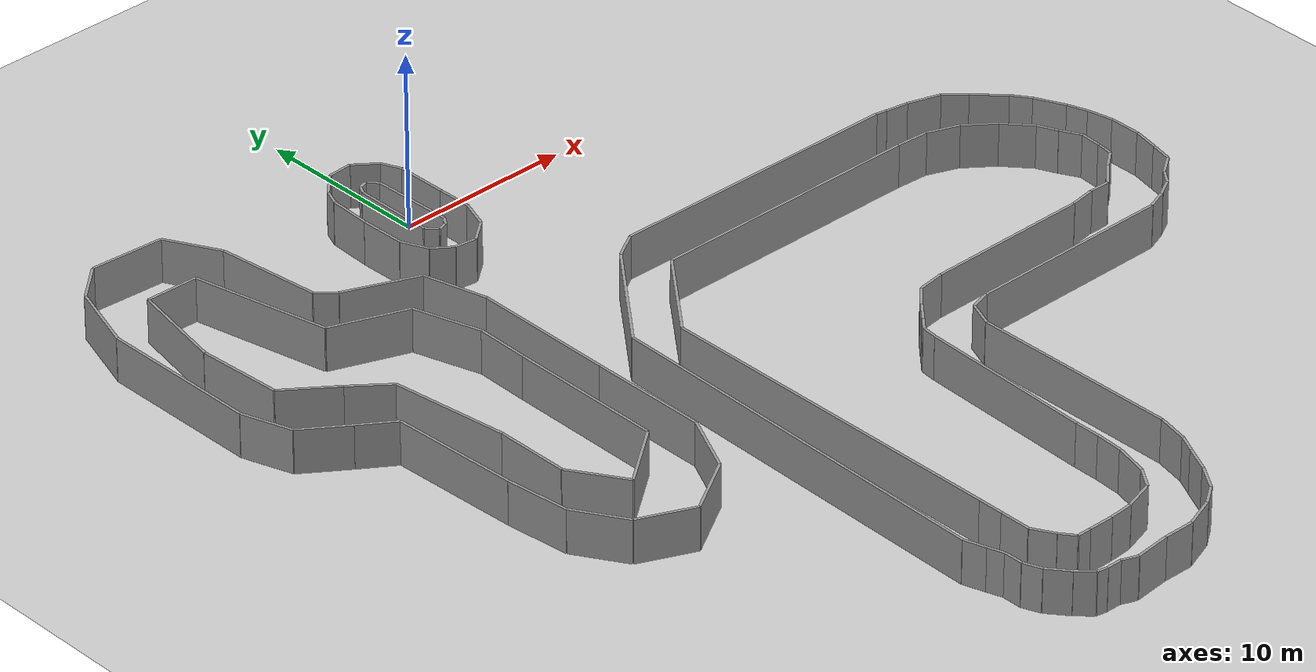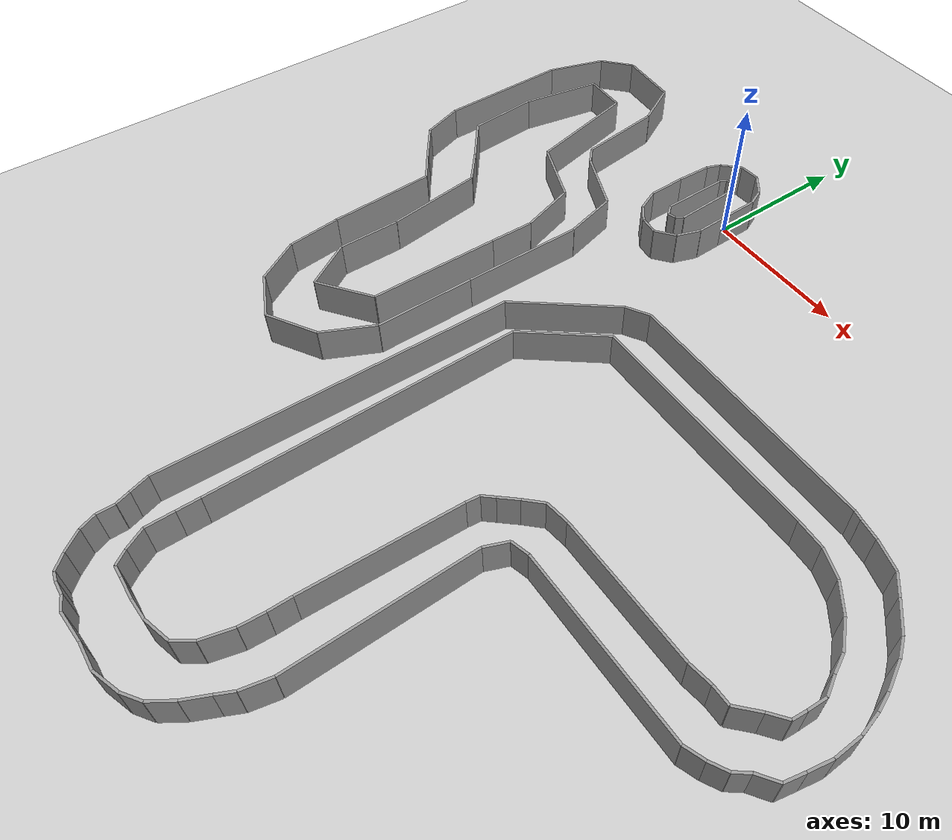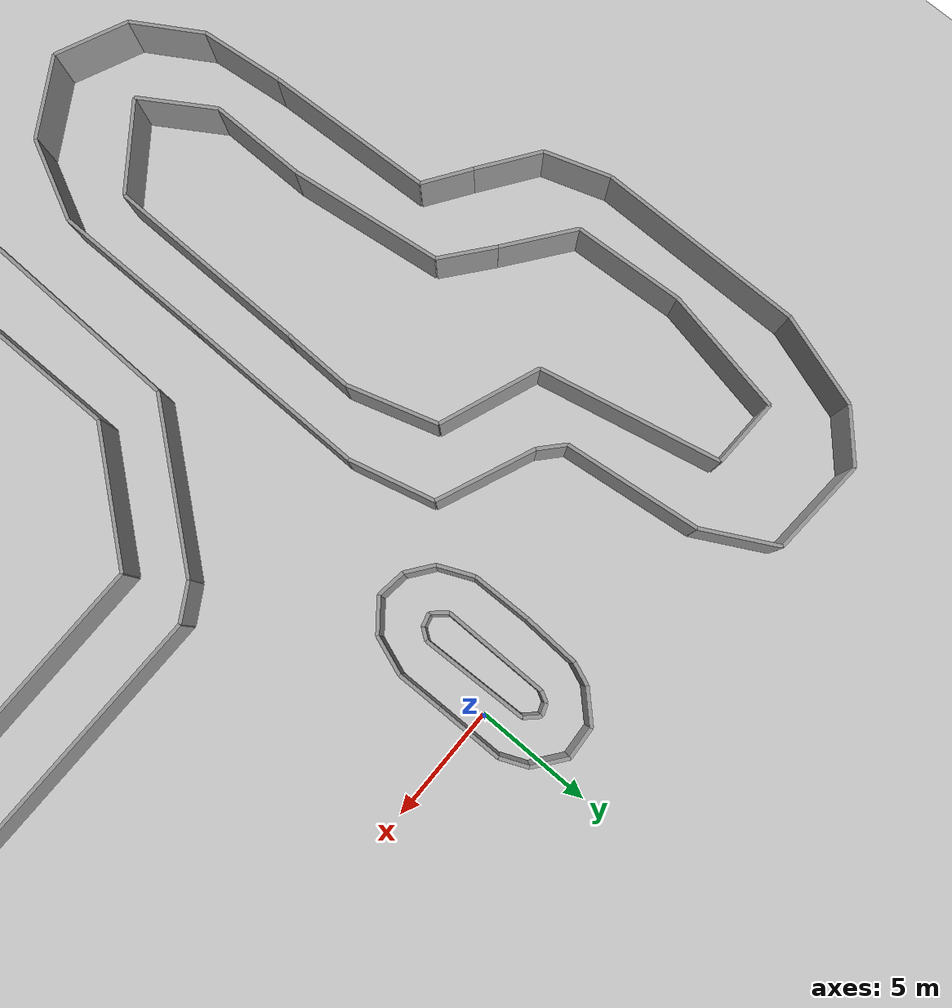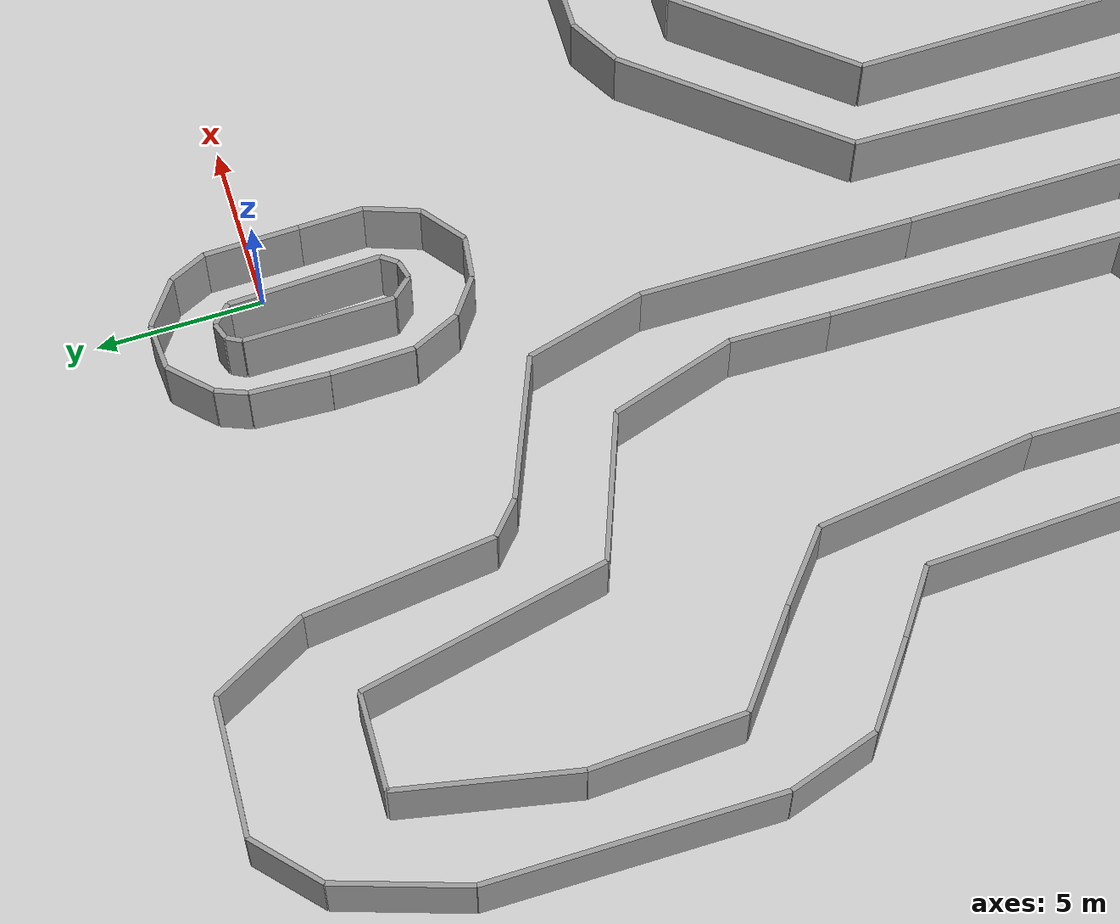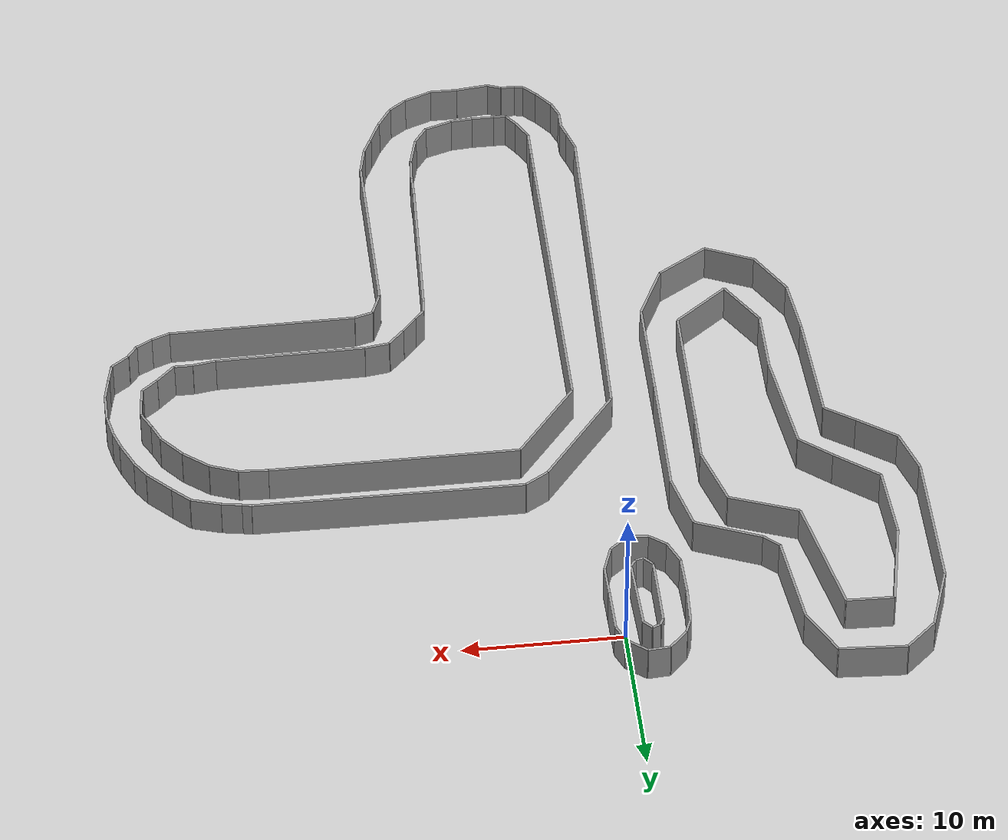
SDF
<sdf version='1.6'>
    <world name='default'>
      <light name='sun' type='directional'>
        <cast_shadows>1</cast_shadows>
        <pose frame=''>0 0 10 0 -0 0</pose>
        <diffuse>0.8 0.8 0.8 1</diffuse>
        <specular>0.2 0.2 0.2 1</specular>
        <attenuation>
          <range>1000</range>
          <constant>0.9</constant>
          <linear>0.01</linear>
          <quadratic>0.001</quadratic>
        </attenuation>
        <direction>-0.5 0.1 -0.9</direction>
      </light>
      <model name='ground_plane'>
        <static>1</static>
        <link name='link'>
          <collision name='collision'>
            <geometry>
              <plane>
                <normal>0 0 1</normal>
                <size>100 100</size>
              </plane>
            </geometry>
            <surface>
              <friction>
                <ode>
                  <mu>100</mu>
                  <mu2>50</mu2>
                </ode>
                <torsional>
                  <ode/>
                </torsional>
              </friction>
              <contact>
                <ode/>
              </contact>
              <bounce/>
            </surface>
            <max_contacts>10</max_contacts>
          </collision>
          <visual name='visual'>
            <cast_shadows>0</cast_shadows>
            <geometry>
              <plane>
                <normal>0 0 1</normal>
                <size>100 100</size>
              </plane>
            </geometry>
            <material>
              <script>
                <uri>file://media/materials/scripts/gazebo.material</uri>
                <name>Gazebo/Grey</name>
              </script>
            </material>
          </visual>
          <self_collide>0</self_collide>
          <enable_wind>0</enable_wind>
          <kinematic>0</kinematic>
        </link>
      </model>
      <gravity>0 0 -9.8</gravity>
      <magnetic_field>6e-06 2.3e-05 -4.2e-05</magnetic_field>
      <atmosphere type='adiabatic'/>
      <physics name='default_physics' default='0' type='ode'>
        <max_step_size>0.001</max_step_size>
        <real_time_factor>1</real_time_factor>
        <real_time_update_rate>1000</real_time_update_rate>
      </physics>
      <scene>
        <ambient>0.4 0.4 0.4 1</ambient>
        <background>0.7 0.7 0.7 1</background>
        <shadows>1</shadows>
      </scene>
      <wind/>
      <spherical_coordinates>
        <surface_model>EARTH_WGS84</surface_model>
        <latitude_deg>0</latitude_deg>
        <longitude_deg>0</longitude_deg>
        <elevation>0</elevation>
        <heading_deg>0</heading_deg>
      </spherical_coordinates>
      <model name='track2'>
        <pose frame=''>0 0 0 0 -0 0</pose>
        <link name='wall_000'>
                <collision name='wall_000_Collision'>
                <geometry>
                    <box>
                    <size>4.375392 0.15 2.5</size>
                    </box>
                </geometry>
                <pose frame=''>0 0 1.25 0 -0 0</pose>
                <max_contacts>10</max_contacts>
                <surface>
                    <contact>
                    <ode/>
                    </contact>
                    <bounce/>
                    <friction>
                    <torsional>
                        <ode/>
                    </torsional>
                    <ode/>
                    </friction>
                </surface>
                </collision>
                <visual name='wall_000_Visual'>
                <pose frame=''>0 0 1.25 0 -0 0</pose>
                <geometry>
                    <box>
                    <size>4.375392 0.15 2.5</size>
                    </box>
                </geometry>
                <material>
                    <script>
                    <uri>file://media/materials/scripts/gazebo.material</uri>
                    <name>Gazebo/Grey</name>
                    </script>
                    <ambient>1 1 1 1</ambient>
                </material>
                <meta>
                    <layer>0</layer>
                </meta>
                </visual>
                <pose frame=''>-6.965100 -5.833000 0 0 -0 -0.390624</pose>
                <self_collide>0</self_collide>
                <enable_wind>0</enable_wind>
                <kinematic>0</kinematic>
            </link>
            <link name='wall_001'>
                <collision name='wall_001_Collision'>
                <geometry>
                    <box>
                    <size>1.246207 0.15 2.5</size>
                    </box>
                </geometry>
                <pose frame=''>0 0 1.25 0 -0 0</pose>
                <max_contacts>10</max_contacts>
                <surface>
                    <contact>
                    <ode/>
                    </contact>
                    <bounce/>
                    <friction>
                    <torsional>
                        <ode/>
                    </torsional>
                    <ode/>
                    </friction>
                </surface>
                </collision>
                <visual name='wall_001_Visual'>
                <pose frame=''>0 0 1.25 0 -0 0</pose>
                <geometry>
                    <box>
                    <size>1.246207 0.15 2.5</size>
                    </box>
                </geometry>
                <material>
                    <script>
                    <uri>file://media/materials/scripts/gazebo.material</uri>
                    <name>Gazebo/Grey</name>
                    </script>
                    <ambient>1 1 1 1</ambient>
                </material>
                <meta>
                    <layer>0</layer>
                </meta>
                </visual>
                <pose frame=''>-9.451000 -4.583000 0 0 -0 -0.733173</pose>
                <self_collide>0</self_collide>
                <enable_wind>0</enable_wind>
                <kinematic>0</kinematic>
            </link>
            <link name='wall_002'>
                <collision name='wall_002_Collision'>
                <geometry>
                    <box>
                    <size>5.872911 0.15 2.5</size>
                    </box>
                </geometry>
                <pose frame=''>0 0 1.25 0 -0 0</pose>
                <max_contacts>10</max_contacts>
                <surface>
                    <contact>
                    <ode/>
                    </contact>
                    <bounce/>
                    <friction>
                    <torsional>
                        <ode/>
                    </torsional>
                    <ode/>
                    </friction>
                </surface>
                </collision>
                <visual name='wall_002_Visual'>
                <pose frame=''>0 0 1.25 0 -0 0</pose>
                <geometry>
                    <box>
                    <size>5.872911 0.15 2.5</size>
                    </box>
                </geometry>
                <material>
                    <script>
                    <uri>file://media/materials/scripts/gazebo.material</uri>
                    <name>Gazebo/Grey</name>
                    </script>
                    <ambient>1 1 1 1</ambient>
                </material>
                <meta>
                    <layer>0</layer>
                </meta>
                </visual>
                <pose frame=''>-10.260000 -1.250000 0 0 -0 -1.452693</pose>
                <self_collide>0</self_collide>
                <enable_wind>0</enable_wind>
                <kinematic>0</kinematic>
            </link>
            <link name='wall_003'>
                <collision name='wall_003_Collision'>
                <geometry>
                    <box>
                    <size>3.309769 0.15 2.5</size>
                    </box>
                </geometry>
                <pose frame=''>0 0 1.25 0 -0 0</pose>
                <max_contacts>10</max_contacts>
                <surface>
                    <contact>
                    <ode/>
                    </contact>
                    <bounce/>
                    <friction>
                    <torsional>
                        <ode/>
                    </torsional>
                    <ode/>
                    </friction>
                </surface>
                </collision>
                <visual name='wall_003_Visual'>
                <pose frame=''>0 0 1.25 0 -0 0</pose>
                <geometry>
                    <box>
                    <size>3.309769 0.15 2.5</size>
                    </box>
                </geometry>
                <material>
                    <script>
                    <uri>file://media/materials/scripts/gazebo.material</uri>
                    <name>Gazebo/Grey</name>
                    </script>
                    <ambient>1 1 1 1</ambient>
                </material>
                <meta>
                    <layer>0</layer>
                </meta>
                </visual>
                <pose frame=''>-11.387000 3.125000 0 0 -0 -1.079311</pose>
                <self_collide>0</self_collide>
                <enable_wind>0</enable_wind>
                <kinematic>0</kinematic>
            </link>
            <link name='wall_004'>
                <collision name='wall_004_Collision'>
                <geometry>
                    <box>
                    <size>4.169502 0.15 2.5</size>
                    </box>
                </geometry>
                <pose frame=''>0 0 1.25 0 -0 0</pose>
                <max_contacts>10</max_contacts>
                <surface>
                    <contact>
                    <ode/>
                    </contact>
                    <bounce/>
                    <friction>
                    <torsional>
                        <ode/>
                    </torsional>
                    <ode/>
                    </friction>
                </surface>
                </collision>
                <visual name='wall_004_Visual'>
                <pose frame=''>0 0 1.25 0 -0 0</pose>
                <geometry>
                    <box>
                    <size>4.169502 0.15 2.5</size>
                    </box>
                </geometry>
                <material>
                    <script>
                    <uri>file://media/materials/scripts/gazebo.material</uri>
                    <name>Gazebo/Grey</name>
                    </script>
                    <ambient>1 1 1 1</ambient>
                </material>
                <meta>
                    <layer>0</layer>
                </meta>
                </visual>
                <pose frame=''>-14.249000 4.709000 0 0 -0 -0.059995</pose>
                <self_collide>0</self_collide>
                <enable_wind>0</enable_wind>
                <kinematic>0</kinematic>
            </link>
            <link name='wall_005'>
                <collision name='wall_005_Collision'>
                <geometry>
                    <box>
                    <size>2.490928 0.15 2.5</size>
                    </box>
                </geometry>
                <pose frame=''>0 0 1.25 0 -0 0</pose>
                <max_contacts>10</max_contacts>
                <surface>
                    <contact>
                    <ode/>
                    </contact>
                    <bounce/>
                    <friction>
                    <torsional>
                        <ode/>
                    </torsional>
                    <ode/>
                    </friction>
                </surface>
                </collision>
                <visual name='wall_005_Visual'>
                <pose frame=''>0 0 1.25 0 -0 0</pose>
                <geometry>
                    <box>
                    <size>2.490928 0.15 2.5</size>
                    </box>
                </geometry>
                <material>
                    <script>
                    <uri>file://media/materials/scripts/gazebo.material</uri>
                    <name>Gazebo/Grey</name>
                    </script>
                    <ambient>1 1 1 1</ambient>
                </material>
                <meta>
                    <layer>0</layer>
                </meta>
                </visual>
                <pose frame=''>-17.255000 4.000000 0 0 -0 0.733710</pose>
                <self_collide>0</self_collide>
                <enable_wind>0</enable_wind>
                <kinematic>0</kinematic>
            </link>
            <link name='wall_006'>
                <collision name='wall_006_Collision'>
                <geometry>
                    <box>
                    <size>4.116790 0.15 2.5</size>
                    </box>
                </geometry>
                <pose frame=''>0 0 1.25 0 -0 0</pose>
                <max_contacts>10</max_contacts>
                <surface>
                    <contact>
                    <ode/>
                    </contact>
                    <bounce/>
                    <friction>
                    <torsional>
                        <ode/>
                    </torsional>
                    <ode/>
                    </friction>
                </surface>
                </collision>
                <visual name='wall_006_Visual'>
                <pose frame=''>0 0 1.25 0 -0 0</pose>
                <geometry>
                    <box>
                    <size>4.116790 0.15 2.5</size>
                    </box>
                </geometry>
                <material>
                    <script>
                    <uri>file://media/materials/scripts/gazebo.material</uri>
                    <name>Gazebo/Grey</name>
                    </script>
                    <ambient>1 1 1 1</ambient>
                </material>
                <meta>
                    <layer>0</layer>
                </meta>
                </visual>
                <pose frame=''>-18.815000 1.208000 0 0 -0 1.257188</pose>
                <self_collide>0</self_collide>
                <enable_wind>0</enable_wind>
                <kinematic>0</kinematic>
            </link>
            <link name='wall_007'>
                <collision name='wall_007_Collision'>
                <geometry>
                    <box>
                    <size>9.000174 0.15 2.5</size>
                    </box>
                </geometry>
                <pose frame=''>0 0 1.25 0 -0 0</pose>
                <max_contacts>10</max_contacts>
                <surface>
                    <contact>
                    <ode/>
                    </contact>
                    <bounce/>
                    <friction>
                    <torsional>
                        <ode/>
                    </torsional>
                    <ode/>
                    </friction>
                </surface>
                </collision>
                <visual name='wall_007_Visual'>
                <pose frame=''>0 0 1.25 0 -0 0</pose>
                <geometry>
                    <box>
                    <size>9.000174 0.15 2.5</size>
                    </box>
                </geometry>
                <material>
                    <script>
                    <uri>file://media/materials/scripts/gazebo.material</uri>
                    <name>Gazebo/Grey</name>
                    </script>
                    <ambient>1 1 1 1</ambient>
                </material>
                <meta>
                    <layer>0</layer>
                </meta>
                </visual>
                <pose frame=''>-19.422000 -5.250000 0 0 -0 1.577018</pose>
                <self_collide>0</self_collide>
                <enable_wind>0</enable_wind>
                <kinematic>0</kinematic>
            </link>
            <link name='wall_008'>
                <collision name='wall_008_Collision'>
                <geometry>
                    <box>
                    <size>2.901719 0.15 2.5</size>
                    </box>
                </geometry>
                <pose frame=''>0 0 1.25 0 -0 0</pose>
                <max_contacts>10</max_contacts>
                <surface>
                    <contact>
                    <ode/>
                    </contact>
                    <bounce/>
                    <friction>
                    <torsional>
                        <ode/>
                    </torsional>
                    <ode/>
                    </friction>
                </surface>
                </collision>
                <visual name='wall_008_Visual'>
                <pose frame=''>0 0 1.25 0 -0 0</pose>
                <geometry>
                    <box>
                    <size>2.901719 0.15 2.5</size>
                    </box>
                </geometry>
                <material>
                    <script>
                    <uri>file://media/materials/scripts/gazebo.material</uri>
                    <name>Gazebo/Grey</name>
                    </script>
                    <ambient>1 1 1 1</ambient>
                </material>
                <meta>
                    <layer>0</layer>
                </meta>
                </visual>
                <pose frame=''>-18.931000 -11.125000 0 0 -0 1.895598</pose>
                <self_collide>0</self_collide>
                <enable_wind>0</enable_wind>
                <kinematic>0</kinematic>
            </link>
            <link name='wall_009'>
                <collision name='wall_009_Collision'>
                <geometry>
                    <box>
                    <size>2.897319 0.15 2.5</size>
                    </box>
                </geometry>
                <pose frame=''>0 0 1.25 0 -0 0</pose>
                <max_contacts>10</max_contacts>
                <surface>
                    <contact>
                    <ode/>
                    </contact>
                    <bounce/>
                    <friction>
                    <torsional>
                        <ode/>
                    </torsional>
                    <ode/>
                    </friction>
                </surface>
                </collision>
                <visual name='wall_009_Visual'>
                <pose frame=''>0 0 1.25 0 -0 0</pose>
                <geometry>
                    <box>
                    <size>2.897319 0.15 2.5</size>
                    </box>
                </geometry>
                <material>
                    <script>
                    <uri>file://media/materials/scripts/gazebo.material</uri>
                    <name>Gazebo/Grey</name>
                    </script>
                    <ambient>1 1 1 1</ambient>
                </material>
                <meta>
                    <layer>0</layer>
                </meta>
                </visual>
                <pose frame=''>-17.283000 -13.333300 0 0 -0 2.528718</pose>
                <self_collide>0</self_collide>
                <enable_wind>0</enable_wind>
                <kinematic>0</kinematic>
            </link>
            <link name='wall_010'>
                <collision name='wall_010_Collision'>
                <geometry>
                    <box>
                    <size>2.232711 0.15 2.5</size>
                    </box>
                </geometry>
                <pose frame=''>0 0 1.25 0 -0 0</pose>
                <max_contacts>10</max_contacts>
                <surface>
                    <contact>
                    <ode/>
                    </contact>
                    <bounce/>
                    <friction>
                    <torsional>
                        <ode/>
                    </torsional>
                    <ode/>
                    </friction>
                </surface>
                </collision>
                <visual name='wall_010_Visual'>
                <pose frame=''>0 0 1.25 0 -0 0</pose>
                <geometry>
                    <box>
                    <size>2.232711 0.15 2.5</size>
                    </box>
                </geometry>
                <material>
                    <script>
                    <uri>file://media/materials/scripts/gazebo.material</uri>
                    <name>Gazebo/Grey</name>
                    </script>
                    <ambient>1 1 1 1</ambient>
                </material>
                <meta>
                    <layer>0</layer>
                </meta>
                </visual>
                <pose frame=''>-15.173000 -14.791600 0 0 -0 2.547379</pose>
                <self_collide>0</self_collide>
                <enable_wind>0</enable_wind>
                <kinematic>0</kinematic>
            </link>
            <link name='wall_011'>
                <collision name='wall_011_Collision'>
                <geometry>
                    <box>
                    <size>7.257652 0.15 2.5</size>
                    </box>
                </geometry>
                <pose frame=''>0 0 1.25 0 -0 0</pose>
                <max_contacts>10</max_contacts>
                <surface>
                    <contact>
                    <ode/>
                    </contact>
                    <bounce/>
                    <friction>
                    <torsional>
                        <ode/>
                    </torsional>
                    <ode/>
                    </friction>
                </surface>
                </collision>
                <visual name='wall_011_Visual'>
                <pose frame=''>0 0 1.25 0 -0 0</pose>
                <geometry>
                    <box>
                    <size>7.257652 0.15 2.5</size>
                    </box>
                </geometry>
                <material>
                    <script>
                    <uri>file://media/materials/scripts/gazebo.material</uri>
                    <name>Gazebo/Grey</name>
                    </script>
                    <ambient>1 1 1 1</ambient>
                </material>
                <meta>
                    <layer>0</layer>
                </meta>
                </visual>
                <pose frame=''>-14.075000 -19.041300 0 0 -0 1.618488</pose>
                <self_collide>0</self_collide>
                <enable_wind>0</enable_wind>
                <kinematic>0</kinematic>
            </link>
            <link name='wall_012'>
                <collision name='wall_012_Collision'>
                <geometry>
                    <box>
                    <size>3.606698 0.15 2.5</size>
                    </box>
                </geometry>
                <pose frame=''>0 0 1.25 0 -0 0</pose>
                <max_contacts>10</max_contacts>
                <surface>
                    <contact>
                    <ode/>
                    </contact>
                    <bounce/>
                    <friction>
                    <torsional>
                        <ode/>
                    </torsional>
                    <ode/>
                    </friction>
                </surface>
                </collision>
                <visual name='wall_012_Visual'>
                <pose frame=''>0 0 1.25 0 -0 0</pose>
                <geometry>
                    <box>
                    <size>3.606698 0.15 2.5</size>
                    </box>
                </geometry>
                <material>
                    <script>
                    <uri>file://media/materials/scripts/gazebo.material</uri>
                    <name>Gazebo/Grey</name>
                    </script>
                    <ambient>1 1 1 1</ambient>
                </material>
                <meta>
                    <layer>0</layer>
                </meta>
                </visual>
                <pose frame=''>-13.700000 -24.458000 0 0 -0 1.683046</pose>
                <self_collide>0</self_collide>
                <enable_wind>0</enable_wind>
                <kinematic>0</kinematic>
            </link>
            <link name='wall_013'>
                <collision name='wall_013_Collision'>
                <geometry>
                    <box>
                    <size>3.221519 0.15 2.5</size>
                    </box>
                </geometry>
                <pose frame=''>0 0 1.25 0 -0 0</pose>
                <max_contacts>10</max_contacts>
                <surface>
                    <contact>
                    <ode/>
                    </contact>
                    <bounce/>
                    <friction>
                    <torsional>
                        <ode/>
                    </torsional>
                    <ode/>
                    </friction>
                </surface>
                </collision>
                <visual name='wall_013_Visual'>
                <pose frame=''>0 0 1.25 0 -0 0</pose>
                <geometry>
                    <box>
                    <size>3.221519 0.15 2.5</size>
                    </box>
                </geometry>
                <material>
                    <script>
                    <uri>file://media/materials/scripts/gazebo.material</uri>
                    <name>Gazebo/Grey</name>
                    </script>
                    <ambient>1 1 1 1</ambient>
                </material>
                <meta>
                    <layer>0</layer>
                </meta>
                </visual>
                <pose frame=''>-12.659000 -27.625000 0 0 -0 2.118669</pose>
                <self_collide>0</self_collide>
                <enable_wind>0</enable_wind>
                <kinematic>0</kinematic>
            </link>
            <link name='wall_014'>
                <collision name='wall_014_Collision'>
                <geometry>
                    <box>
                    <size>3.286879 0.15 2.5</size>
                    </box>
                </geometry>
                <pose frame=''>0 0 1.25 0 -0 0</pose>
                <max_contacts>10</max_contacts>
                <surface>
                    <contact>
                    <ode/>
                    </contact>
                    <bounce/>
                    <friction>
                    <torsional>
                        <ode/>
                    </torsional>
                    <ode/>
                    </friction>
                </surface>
                </collision>
                <visual name='wall_014_Visual'>
                <pose frame=''>0 0 1.25 0 -0 0</pose>
                <geometry>
                    <box>
                    <size>3.286879 0.15 2.5</size>
                    </box>
                </geometry>
                <material>
                    <script>
                    <uri>file://media/materials/scripts/gazebo.material</uri>
                    <name>Gazebo/Grey</name>
                    </script>
                    <ambient>1 1 1 1</ambient>
                </material>
                <meta>
                    <layer>0</layer>
                </meta>
                </visual>
                <pose frame=''>-10.318000 -29.667000 0 0 -0 2.723677</pose>
                <self_collide>0</self_collide>
                <enable_wind>0</enable_wind>
                <kinematic>0</kinematic>
            </link>
            <link name='wall_015'>
                <collision name='wall_015_Collision'>
                <geometry>
                    <box>
                    <size>3.664438 0.15 2.5</size>
                    </box>
                </geometry>
                <pose frame=''>0 0 1.25 0 -0 0</pose>
                <max_contacts>10</max_contacts>
                <surface>
                    <contact>
                    <ode/>
                    </contact>
                    <bounce/>
                    <friction>
                    <torsional>
                        <ode/>
                    </torsional>
                    <ode/>
                    </friction>
                </surface>
                </collision>
                <visual name='wall_015_Visual'>
                <pose frame=''>0 0 1.25 0 -0 0</pose>
                <geometry>
                    <box>
                    <size>3.664438 0.15 2.5</size>
                    </box>
                </geometry>
                <material>
                    <script>
                    <uri>file://media/materials/scripts/gazebo.material</uri>
                    <name>Gazebo/Grey</name>
                    </script>
                    <ambient>1 1 1 1</ambient>
                </material>
                <meta>
                    <layer>0</layer>
                </meta>
                </visual>
                <pose frame=''>-7.254800 -29.375000 0 0 -0 -2.590746</pose>
                <self_collide>0</self_collide>
                <enable_wind>0</enable_wind>
                <kinematic>0</kinematic>
            </link>
            <link name='wall_016'>
                <collision name='wall_016_Collision'>
                <geometry>
                    <box>
                    <size>3.704247 0.15 2.5</size>
                    </box>
                </geometry>
                <pose frame=''>0 0 1.25 0 -0 0</pose>
                <max_contacts>10</max_contacts>
                <surface>
                    <contact>
                    <ode/>
                    </contact>
                    <bounce/>
                    <friction>
                    <torsional>
                        <ode/>
                    </torsional>
                    <ode/>
                    </friction>
                </surface>
                </collision>
                <visual name='wall_016_Visual'>
                <pose frame=''>0 0 1.25 0 -0 0</pose>
                <geometry>
                    <box>
                    <size>3.704247 0.15 2.5</size>
                    </box>
                </geometry>
                <material>
                    <script>
                    <uri>file://media/materials/scripts/gazebo.material</uri>
                    <name>Gazebo/Grey</name>
                    </script>
                    <ambient>1 1 1 1</ambient>
                </material>
                <meta>
                    <layer>0</layer>
                </meta>
                </visual>
                <pose frame=''>-4.884400 -26.750000 0 0 -0 -2.022950</pose>
                <self_collide>0</self_collide>
                <enable_wind>0</enable_wind>
                <kinematic>0</kinematic>
            </link>
            <link name='wall_017'>
                <collision name='wall_017_Collision'>
                <geometry>
                    <box>
                    <size>6.668000 0.15 2.5</size>
                    </box>
                </geometry>
                <pose frame=''>0 0 1.25 0 -0 0</pose>
                <max_contacts>10</max_contacts>
                <surface>
                    <contact>
                    <ode/>
                    </contact>
                    <bounce/>
                    <friction>
                    <torsional>
                        <ode/>
                    </torsional>
                    <ode/>
                    </friction>
                </surface>
                </collision>
                <visual name='wall_017_Visual'>
                <pose frame=''>0 0 1.25 0 -0 0</pose>
                <geometry>
                    <box>
                    <size>6.668000 0.15 2.5</size>
                    </box>
                </geometry>
                <material>
                    <script>
                    <uri>file://media/materials/scripts/gazebo.material</uri>
                    <name>Gazebo/Grey</name>
                    </script>
                    <ambient>1 1 1 1</ambient>
                </material>
                <meta>
                    <layer>0</layer>
                </meta>
                </visual>
                <pose frame=''>-4.075200 -21.750000 0 0 -0 -1.570796</pose>
                <self_collide>0</self_collide>
                <enable_wind>0</enable_wind>
                <kinematic>0</kinematic>
            </link>
            <link name='wall_018'>
                <collision name='wall_018_Collision'>
                <geometry>
                    <box>
                    <size>8.166205 0.15 2.5</size>
                    </box>
                </geometry>
                <pose frame=''>0 0 1.25 0 -0 0</pose>
                <max_contacts>10</max_contacts>
                <surface>
                    <contact>
                    <ode/>
                    </contact>
                    <bounce/>
                    <friction>
                    <torsional>
                        <ode/>
                    </torsional>
                    <ode/>
                    </friction>
                </surface>
                </collision>
                <visual name='wall_018_Visual'>
                <pose frame=''>0 0 1.25 0 -0 0</pose>
                <geometry>
                    <box>
                    <size>8.166205 0.15 2.5</size>
                    </box>
                </geometry>
                <material>
                    <script>
                    <uri>file://media/materials/scripts/gazebo.material</uri>
                    <name>Gazebo/Grey</name>
                    </script>
                    <ambient>1 1 1 1</ambient>
                </material>
                <meta>
                    <layer>0</layer>
                </meta>
                </visual>
                <pose frame=''>-4.046300 -14.333000 0 0 -0 -1.577874</pose>
                <self_collide>0</self_collide>
                <enable_wind>0</enable_wind>
                <kinematic>0</kinematic>
            </link>
            <link name='wall_019'>
                <collision name='wall_019_Collision'>
                <geometry>
                    <box>
                    <size>3.701393 0.15 2.5</size>
                    </box>
                </geometry>
                <pose frame=''>0 0 1.25 0 -0 0</pose>
                <max_contacts>10</max_contacts>
                <surface>
                    <contact>
                    <ode/>
                    </contact>
                    <bounce/>
                    <friction>
                    <torsional>
                        <ode/>
                    </torsional>
                    <ode/>
                    </friction>
                </surface>
                </collision>
                <visual name='wall_019_Visual'>
                <pose frame=''>0 0 1.25 0 -0 0</pose>
                <geometry>
                    <box>
                    <size>3.701393 0.15 2.5</size>
                    </box>
                </geometry>
                <material>
                    <script>
                    <uri>file://media/materials/scripts/gazebo.material</uri>
                    <name>Gazebo/Grey</name>
                    </script>
                    <ambient>1 1 1 1</ambient>
                </material>
                <meta>
                    <layer>0</layer>
                </meta>
                </visual>
                <pose frame=''>-4.479800 -8.458000 0 0 -0 -1.318269</pose>
                <self_collide>0</self_collide>
                <enable_wind>0</enable_wind>
                <kinematic>0</kinematic>
            </link>
            <link name='wall_020'>
                <collision name='wall_020_Collision'>
                <geometry>
                    <box>
                    <size>4.507489 0.15 2.5</size>
                    </box>
                </geometry>
                <pose frame=''>0 0 1.25 0 -0 0</pose>
                <max_contacts>10</max_contacts>
                <surface>
                    <contact>
                    <ode/>
                    </contact>
                    <bounce/>
                    <friction>
                    <torsional>
                        <ode/>
                    </torsional>
                    <ode/>
                    </friction>
                </surface>
                </collision>
                <visual name='wall_020_Visual'>
                <pose frame=''>0 0 1.25 0 -0 0</pose>
                <geometry>
                    <box>
                    <size>4.507489 0.15 2.5</size>
                    </box>
                </geometry>
                <material>
                    <script>
                    <uri>file://media/materials/scripts/gazebo.material</uri>
                    <name>Gazebo/Grey</name>
                    </script>
                    <ambient>1 1 1 1</ambient>
                </material>
                <meta>
                    <layer>0</layer>
                </meta>
                </visual>
                <pose frame=''>-9.422000 -7.708000 0 0 -0 -0.359082</pose>
                <self_collide>0</self_collide>
                <enable_wind>0</enable_wind>
                <kinematic>0</kinematic>
            </link>
            <link name='wall_021'>
                <collision name='wall_021_Collision'>
                <geometry>
                    <box>
                    <size>7.847072 0.15 2.5</size>
                    </box>
                </geometry>
                <pose frame=''>0 0 1.25 0 -0 0</pose>
                <max_contacts>10</max_contacts>
                <surface>
                    <contact>
                    <ode/>
                    </contact>
                    <bounce/>
                    <friction>
                    <torsional>
                        <ode/>
                    </torsional>
                    <ode/>
                    </friction>
                </surface>
                </collision>
                <visual name='wall_021_Visual'>
                <pose frame=''>0 0 1.25 0 -0 0</pose>
                <geometry>
                    <box>
                    <size>7.847072 0.15 2.5</size>
                    </box>
                </geometry>
                <material>
                    <script>
                    <uri>file://media/materials/scripts/gazebo.material</uri>
                    <name>Gazebo/Grey</name>
                    </script>
                    <ambient>1 1 1 1</ambient>
                </material>
                <meta>
                    <layer>0</layer>
                </meta>
                </visual>
                <pose frame=''>-12.370000 -3.083000 0 0 -0 -1.355555</pose>
                <self_collide>0</self_collide>
                <enable_wind>0</enable_wind>
                <kinematic>0</kinematic>
            </link>
            <link name='wall_022'>
                <collision name='wall_022_Collision'>
                <geometry>
                    <box>
                    <size>2.949197 0.15 2.5</size>
                    </box>
                </geometry>
                <pose frame=''>0 0 1.25 0 -0 0</pose>
                <max_contacts>10</max_contacts>
                <surface>
                    <contact>
                    <ode/>
                    </contact>
                    <bounce/>
                    <friction>
                    <torsional>
                        <ode/>
                    </torsional>
                    <ode/>
                    </friction>
                </surface>
                </collision>
                <visual name='wall_022_Visual'>
                <pose frame=''>0 0 1.25 0 -0 0</pose>
                <geometry>
                    <box>
                    <size>2.949197 0.15 2.5</size>
                    </box>
                </geometry>
                <material>
                    <script>
                    <uri>file://media/materials/scripts/gazebo.material</uri>
                    <name>Gazebo/Grey</name>
                    </script>
                    <ambient>1 1 1 1</ambient>
                </material>
                <meta>
                    <layer>0</layer>
                </meta>
                </visual>
                <pose frame=''>-14.682000 0.792000 0 0 -0 -0.028486</pose>
                <self_collide>0</self_collide>
                <enable_wind>0</enable_wind>
                <kinematic>0</kinematic>
            </link>
            <link name='wall_023'>
                <collision name='wall_023_Collision'>
                <geometry>
                    <box>
                    <size>5.516913 0.15 2.5</size>
                    </box>
                </geometry>
                <pose frame=''>0 0 1.25 0 -0 0</pose>
                <max_contacts>10</max_contacts>
                <surface>
                    <contact>
                    <ode/>
                    </contact>
                    <bounce/>
                    <friction>
                    <torsional>
                        <ode/>
                    </torsional>
                    <ode/>
                    </friction>
                </surface>
                </collision>
                <visual name='wall_023_Visual'>
                <pose frame=''>0 0 1.25 0 -0 0</pose>
                <geometry>
                    <box>
                    <size>5.516913 0.15 2.5</size>
                    </box>
                </geometry>
                <material>
                    <script>
                    <uri>file://media/materials/scripts/gazebo.material</uri>
                    <name>Gazebo/Grey</name>
                    </script>
                    <ambient>1 1 1 1</ambient>
                </material>
                <meta>
                    <layer>0</layer>
                </meta>
                </visual>
                <pose frame=''>-16.676000 -1.875000 0 0 -0 1.381150</pose>
                <self_collide>0</self_collide>
                <enable_wind>0</enable_wind>
                <kinematic>0</kinematic>
            </link>
            <link name='wall_024'>
                <collision name='wall_024_Collision'>
                <geometry>
                    <box>
                    <size>4.758723 0.15 2.5</size>
                    </box>
                </geometry>
                <pose frame=''>0 0 1.25 0 -0 0</pose>
                <max_contacts>10</max_contacts>
                <surface>
                    <contact>
                    <ode/>
                    </contact>
                    <bounce/>
                    <friction>
                    <torsional>
                        <ode/>
                    </torsional>
                    <ode/>
                    </friction>
                </surface>
                </collision>
                <visual name='wall_024_Visual'>
                <pose frame=''>0 0 1.25 0 -0 0</pose>
                <geometry>
                    <box>
                    <size>4.758723 0.15 2.5</size>
                    </box>
                </geometry>
                <material>
                    <script>
                    <uri>file://media/materials/scripts/gazebo.material</uri>
                    <name>Gazebo/Grey</name>
                    </script>
                    <ambient>1 1 1 1</ambient>
                </material>
                <meta>
                    <layer>0</layer>
                </meta>
                </visual>
                <pose frame=''>-17.052000 -6.959000 0 0 -0 1.631354</pose>
                <self_collide>0</self_collide>
                <enable_wind>0</enable_wind>
                <kinematic>0</kinematic>
            </link>
            <link name='wall_025'>
                <collision name='wall_025_Collision'>
                <geometry>
                    <box>
                    <size>3.328002 0.15 2.5</size>
                    </box>
                </geometry>
                <pose frame=''>0 0 1.25 0 -0 0</pose>
                <max_contacts>10</max_contacts>
                <surface>
                    <contact>
                    <ode/>
                    </contact>
                    <bounce/>
                    <friction>
                    <torsional>
                        <ode/>
                    </torsional>
                    <ode/>
                    </friction>
                </surface>
                </collision>
                <visual name='wall_025_Visual'>
                <pose frame=''>0 0 1.25 0 -0 0</pose>
                <geometry>
                    <box>
                    <size>3.328002 0.15 2.5</size>
                    </box>
                </geometry>
                <material>
                    <script>
                    <uri>file://media/materials/scripts/gazebo.material</uri>
                    <name>Gazebo/Grey</name>
                    </script>
                    <ambient>1 1 1 1</ambient>
                </material>
                <meta>
                    <layer>0</layer>
                </meta>
                </visual>
                <pose frame=''>-15.578000 -10.334000 0 0 -0 2.496890</pose>
                <self_collide>0</self_collide>
                <enable_wind>0</enable_wind>
                <kinematic>0</kinematic>
            </link>
            <link name='wall_026'>
                <collision name='wall_026_Collision'>
                <geometry>
                    <box>
                    <size>2.521908 0.15 2.5</size>
                    </box>
                </geometry>
                <pose frame=''>0 0 1.25 0 -0 0</pose>
                <max_contacts>10</max_contacts>
                <surface>
                    <contact>
                    <ode/>
                    </contact>
                    <bounce/>
                    <friction>
                    <torsional>
                        <ode/>
                    </torsional>
                    <ode/>
                    </friction>
                </surface>
                </collision>
                <visual name='wall_026_Visual'>
                <pose frame=''>0 0 1.25 0 -0 0</pose>
                <geometry>
                    <box>
                    <size>2.521908 0.15 2.5</size>
                    </box>
                </geometry>
                <material>
                    <script>
                    <uri>file://media/materials/scripts/gazebo.material</uri>
                    <name>Gazebo/Grey</name>
                    </script>
                    <ambient>1 1 1 1</ambient>
                </material>
                <meta>
                    <layer>0</layer>
                </meta>
                </visual>
                <pose frame=''>-13.266000 -12.125000 0 0 -0 2.463508</pose>
                <self_collide>0</self_collide>
                <enable_wind>0</enable_wind>
                <kinematic>0</kinematic>
            </link>
            <link name='wall_027'>
                <collision name='wall_027_Collision'>
                <geometry>
                    <box>
                    <size>6.640970 0.15 2.5</size>
                    </box>
                </geometry>
                <pose frame=''>0 0 1.25 0 -0 0</pose>
                <max_contacts>10</max_contacts>
                <surface>
                    <contact>
                    <ode/>
                    </contact>
                    <bounce/>
                    <friction>
                    <torsional>
                        <ode/>
                    </torsional>
                    <ode/>
                    </friction>
                </surface>
                </collision>
                <visual name='wall_027_Visual'>
                <pose frame=''>0 0 1.25 0 -0 0</pose>
                <geometry>
                    <box>
                    <size>6.640970 0.15 2.5</size>
                    </box>
                </geometry>
                <material>
                    <script>
                    <uri>file://media/materials/scripts/gazebo.material</uri>
                    <name>Gazebo/Grey</name>
                    </script>
                    <ambient>1 1 1 1</ambient>
                </material>
                <meta>
                    <layer>0</layer>
                </meta>
                </visual>
                <pose frame=''>-11.850000 -16.208000 0 0 -0 1.701875</pose>
                <self_collide>0</self_collide>
                <enable_wind>0</enable_wind>
                <kinematic>0</kinematic>
            </link>
            <link name='wall_028'>
                <collision name='wall_028_Collision'>
                <geometry>
                    <box>
                    <size>4.166000 0.15 2.5</size>
                    </box>
                </geometry>
                <pose frame=''>0 0 1.25 0 -0 0</pose>
                <max_contacts>10</max_contacts>
                <surface>
                    <contact>
                    <ode/>
                    </contact>
                    <bounce/>
                    <friction>
                    <torsional>
                        <ode/>
                    </torsional>
                    <ode/>
                    </friction>
                </surface>
                </collision>
                <visual name='wall_028_Visual'>
                <pose frame=''>0 0 1.25 0 -0 0</pose>
                <geometry>
                    <box>
                    <size>4.166000 0.15 2.5</size>
                    </box>
                </geometry>
                <material>
                    <script>
                    <uri>file://media/materials/scripts/gazebo.material</uri>
                    <name>Gazebo/Grey</name>
                    </script>
                    <ambient>1 1 1 1</ambient>
                </material>
                <meta>
                    <layer>0</layer>
                </meta>
                </visual>
                <pose frame=''>-11.416000 -21.583000 0 0 -0 1.570796</pose>
                <self_collide>0</self_collide>
                <enable_wind>0</enable_wind>
                <kinematic>0</kinematic>
            </link>
            <link name='wall_029'>
                <collision name='wall_029_Collision'>
                <geometry>
                    <box>
                    <size>3.455029 0.15 2.5</size>
                    </box>
                </geometry>
                <pose frame=''>0 0 1.25 0 -0 0</pose>
                <max_contacts>10</max_contacts>
                <surface>
                    <contact>
                    <ode/>
                    </contact>
                    <bounce/>
                    <friction>
                    <torsional>
                        <ode/>
                    </torsional>
                    <ode/>
                    </friction>
                </surface>
                </collision>
                <visual name='wall_029_Visual'>
                <pose frame=''>0 0 1.25 0 -0 0</pose>
                <geometry>
                    <box>
                    <size>3.455029 0.15 2.5</size>
                    </box>
                </geometry>
                <material>
                    <script>
                    <uri>file://media/materials/scripts/gazebo.material</uri>
                    <name>Gazebo/Grey</name>
                    </script>
                    <ambient>1 1 1 1</ambient>
                </material>
                <meta>
                    <layer>0</layer>
                </meta>
                </visual>
                <pose frame=''>-10.491000 -25.125000 0 0 -0 2.135838</pose>
                <self_collide>0</self_collide>
                <enable_wind>0</enable_wind>
                <kinematic>0</kinematic>
            </link>
            <link name='wall_030'>
                <collision name='wall_030_Collision'>
                <geometry>
                    <box>
                    <size>4.135586 0.15 2.5</size>
                    </box>
                </geometry>
                <pose frame=''>0 0 1.25 0 -0 0</pose>
                <max_contacts>10</max_contacts>
                <surface>
                    <contact>
                    <ode/>
                    </contact>
                    <bounce/>
                    <friction>
                    <torsional>
                        <ode/>
                    </torsional>
                    <ode/>
                    </friction>
                </surface>
                </collision>
                <visual name='wall_030_Visual'>
                <pose frame=''>0 0 1.25 0 -0 0</pose>
                <geometry>
                    <box>
                    <size>4.135586 0.15 2.5</size>
                    </box>
                </geometry>
                <material>
                    <script>
                    <uri>file://media/materials/scripts/gazebo.material</uri>
                    <name>Gazebo/Grey</name>
                    </script>
                    <ambient>1 1 1 1</ambient>
                </material>
                <meta>
                    <layer>0</layer>
                </meta>
                </visual>
                <pose frame=''>-7.918800 -25.334000 0 0 -0 -2.492443</pose>
                <self_collide>0</self_collide>
                <enable_wind>0</enable_wind>
                <kinematic>0</kinematic>
            </link>
            <link name='wall_031'>
                <collision name='wall_031_Collision'>
                <geometry>
                    <box>
                    <size>8.834189 0.15 2.5</size>
                    </box>
                </geometry>
                <pose frame=''>0 0 1.25 0 -0 0</pose>
                <max_contacts>10</max_contacts>
                <surface>
                    <contact>
                    <ode/>
                    </contact>
                    <bounce/>
                    <friction>
                    <torsional>
                        <ode/>
                    </torsional>
                    <ode/>
                    </friction>
                </surface>
                </collision>
                <visual name='wall_031_Visual'>
                <pose frame=''>0 0 1.25 0 -0 0</pose>
                <geometry>
                    <box>
                    <size>8.834189 0.15 2.5</size>
                    </box>
                </geometry>
                <material>
                    <script>
                    <uri>file://media/materials/scripts/gazebo.material</uri>
                    <name>Gazebo/Grey</name>
                    </script>
                    <ambient>1 1 1 1</ambient>
                </material>
                <meta>
                    <layer>0</layer>
                </meta>
                </visual>
                <pose frame=''>-6.242700 -19.667000 0 0 -0 -1.577339</pose>
                <self_collide>0</self_collide>
                <enable_wind>0</enable_wind>
                <kinematic>0</kinematic>
            </link>
            <link name='wall_032'>
                <collision name='wall_032_Collision'>
                <geometry>
                    <box>
                    <size>3.000557 0.15 2.5</size>
                    </box>
                </geometry>
                <pose frame=''>0 0 1.25 0 -0 0</pose>
                <max_contacts>10</max_contacts>
                <surface>
                    <contact>
                    <ode/>
                    </contact>
                    <bounce/>
                    <friction>
                    <torsional>
                        <ode/>
                    </torsional>
                    <ode/>
                    </friction>
                </surface>
                </collision>
                <visual name='wall_032_Visual'>
                <pose frame=''>0 0 1.25 0 -0 0</pose>
                <geometry>
                    <box>
                    <size>3.000557 0.15 2.5</size>
                    </box>
                </geometry>
                <material>
                    <script>
                    <uri>file://media/materials/scripts/gazebo.material</uri>
                    <name>Gazebo/Grey</name>
                    </script>
                    <ambient>1 1 1 1</ambient>
                </material>
                <meta>
                    <layer>0</layer>
                </meta>
                </visual>
                <pose frame=''>-6.184900 -13.750000 0 0 -0 -1.590061</pose>
                <self_collide>0</self_collide>
                <enable_wind>0</enable_wind>
                <kinematic>0</kinematic>
            </link>
            <link name='wall_033'>
                <collision name='wall_033_Collision'>
                <geometry>
                    <box>
                    <size>3.924135 0.15 2.5</size>
                    </box>
                </geometry>
                <pose frame=''>0 0 1.25 0 -0 0</pose>
                <max_contacts>10</max_contacts>
                <surface>
                    <contact>
                    <ode/>
                    </contact>
                    <bounce/>
                    <friction>
                    <torsional>
                        <ode/>
                    </torsional>
                    <ode/>
                    </friction>
                </surface>
                </collision>
                <visual name='wall_033_Visual'>
                <pose frame=''>0 0 1.25 0 -0 0</pose>
                <geometry>
                    <box>
                    <size>3.924135 0.15 2.5</size>
                    </box>
                </geometry>
                <material>
                    <script>
                    <uri>file://media/materials/scripts/gazebo.material</uri>
                    <name>Gazebo/Grey</name>
                    </script>
                    <ambient>1 1 1 1</ambient>
                </material>
                <meta>
                    <layer>0</layer>
                </meta>
                </visual>
                <pose frame=''>-6.734000 -10.375000 0 0 -0 -1.271773</pose>
                <self_collide>0</self_collide>
                <enable_wind>0</enable_wind>
                <kinematic>0</kinematic>
            </link>
            <link name='wall_034'>
                <collision name='wall_034_Collision'>
                <geometry>
                    <box>
                    <size>1.195634 0.15 2.5</size>
                    </box>
                </geometry>
                <pose frame=''>0 0 1.25 0 -0 0</pose>
                <max_contacts>10</max_contacts>
                <surface>
                    <contact>
                    <ode/>
                    </contact>
                    <bounce/>
                    <friction>
                    <torsional>
                        <ode/>
                    </torsional>
                    <ode/>
                    </friction>
                </surface>
                </collision>
                <visual name='wall_034_Visual'>
                <pose frame=''>0 0 1.25 0 -0 0</pose>
                <geometry>
                    <box>
                    <size>1.195634 0.15 2.5</size>
                    </box>
                </geometry>
                <material>
                    <script>
                    <uri>file://media/materials/scripts/gazebo.material</uri>
                    <name>Gazebo/Grey</name>
                    </script>
                    <ambient>1 1 1 1</ambient>
                </material>
                <meta>
                    <layer>0</layer>
                </meta>
                </visual>
                <pose frame=''>0.586740 1.912500 0 0 -0 -1.157576</pose>
                <self_collide>0</self_collide>
                <enable_wind>0</enable_wind>
                <kinematic>0</kinematic>
            </link>
            <link name='wall_035'>
                <collision name='wall_035_Collision'>
                <geometry>
                    <box>
                    <size>1.548632 0.15 2.5</size>
                    </box>
                </geometry>
                <pose frame=''>0 0 1.25 0 -0 0</pose>
                <max_contacts>10</max_contacts>
                <surface>
                    <contact>
                    <ode/>
                    </contact>
                    <bounce/>
                    <friction>
                    <torsional>
                        <ode/>
                    </torsional>
                    <ode/>
                    </friction>
                </surface>
                </collision>
                <visual name='wall_035_Visual'>
                <pose frame=''>0 0 1.25 0 -0 0</pose>
                <geometry>
                    <box>
                    <size>1.548632 0.15 2.5</size>
                    </box>
                </geometry>
                <material>
                    <script>
                    <uri>file://media/materials/scripts/gazebo.material</uri>
                    <name>Gazebo/Grey</name>
                    </script>
                    <ambient>1 1 1 1</ambient>
                </material>
                <meta>
                    <layer>0</layer>
                </meta>
                </visual>
                <pose frame=''>-0.266760 2.932500 0 0 -0 -0.656333</pose>
                <self_collide>0</self_collide>
                <enable_wind>0</enable_wind>
                <kinematic>0</kinematic>
            </link>
            <link name='wall_036'>
                <collision name='wall_036_Collision'>
                <geometry>
                    <box>
                    <size>1.362576 0.15 2.5</size>
                    </box>
                </geometry>
                <pose frame=''>0 0 1.25 0 -0 0</pose>
                <max_contacts>10</max_contacts>
                <surface>
                    <contact>
                    <ode/>
                    </contact>
                    <bounce/>
                    <friction>
                    <torsional>
                        <ode/>
                    </torsional>
                    <ode/>
                    </friction>
                </surface>
                </collision>
                <visual name='wall_036_Visual'>
                <pose frame=''>0 0 1.25 0 -0 0</pose>
                <geometry>
                    <box>
                    <size>1.362576 0.15 2.5</size>
                    </box>
                </geometry>
                <material>
                    <script>
                    <uri>file://media/materials/scripts/gazebo.material</uri>
                    <name>Gazebo/Grey</name>
                    </script>
                    <ambient>1 1 1 1</ambient>
                </material>
                <meta>
                    <layer>0</layer>
                </meta>
                </visual>
                <pose frame=''>-1.560000 3.360000 0 0 -0 0.066100</pose>
                <self_collide>0</self_collide>
                <enable_wind>0</enable_wind>
                <kinematic>0</kinematic>
            </link>
            <link name='wall_037'>
                <collision name='wall_037_Collision'>
                <geometry>
                    <box>
                    <size>1.558364 0.15 2.5</size>
                    </box>
                </geometry>
                <pose frame=''>0 0 1.25 0 -0 0</pose>
                <max_contacts>10</max_contacts>
                <surface>
                    <contact>
                    <ode/>
                    </contact>
                    <bounce/>
                    <friction>
                    <torsional>
                        <ode/>
                    </torsional>
                    <ode/>
                    </friction>
                </surface>
                </collision>
                <visual name='wall_037_Visual'>
                <pose frame=''>0 0 1.25 0 -0 0</pose>
                <geometry>
                    <box>
                    <size>1.558364 0.15 2.5</size>
                    </box>
                </geometry>
                <material>
                    <script>
                    <uri>file://media/materials/scripts/gazebo.material</uri>
                    <name>Gazebo/Grey</name>
                    </script>
                    <ambient>1 1 1 1</ambient>
                </material>
                <meta>
                    <layer>0</layer>
                </meta>
                </visual>
                <pose frame=''>-2.786700 2.760000 0 0 -0 0.792749</pose>
                <self_collide>0</self_collide>
                <enable_wind>0</enable_wind>
                <kinematic>0</kinematic>
            </link>
            <link name='wall_038'>
                <collision name='wall_038_Collision'>
                <geometry>
                    <box>
                    <size>0.983273 0.15 2.5</size>
                    </box>
                </geometry>
                <pose frame=''>0 0 1.25 0 -0 0</pose>
                <max_contacts>10</max_contacts>
                <surface>
                    <contact>
                    <ode/>
                    </contact>
                    <bounce/>
                    <friction>
                    <torsional>
                        <ode/>
                    </torsional>
                    <ode/>
                    </friction>
                </surface>
                </collision>
                <visual name='wall_038_Visual'>
                <pose frame=''>0 0 1.25 0 -0 0</pose>
                <geometry>
                    <box>
                    <size>0.983273 0.15 2.5</size>
                    </box>
                </geometry>
                <material>
                    <script>
                    <uri>file://media/materials/scripts/gazebo.material</uri>
                    <name>Gazebo/Grey</name>
                    </script>
                    <ambient>1 1 1 1</ambient>
                </material>
                <meta>
                    <layer>0</layer>
                </meta>
                </visual>
                <pose frame=''>-3.513600 1.747500 0 0 -0 1.195956</pose>
                <self_collide>0</self_collide>
                <enable_wind>0</enable_wind>
                <kinematic>0</kinematic>
            </link>
            <link name='wall_039'>
                <collision name='wall_039_Collision'>
                <geometry>
                    <box>
                    <size>2.372378 0.15 2.5</size>
                    </box>
                </geometry>
                <pose frame=''>0 0 1.25 0 -0 0</pose>
                <max_contacts>10</max_contacts>
                <surface>
                    <contact>
                    <ode/>
                    </contact>
                    <bounce/>
                    <friction>
                    <torsional>
                        <ode/>
                    </torsional>
                    <ode/>
                    </friction>
                </surface>
                </collision>
                <visual name='wall_039_Visual'>
                <pose frame=''>0 0 1.25 0 -0 0</pose>
                <geometry>
                    <box>
                    <size>2.372378 0.15 2.5</size>
                    </box>
                </geometry>
                <material>
                    <script>
                    <uri>file://media/materials/scripts/gazebo.material</uri>
                    <name>Gazebo/Grey</name>
                    </script>
                    <ambient>1 1 1 1</ambient>
                </material>
                <meta>
                    <layer>0</layer>
                </meta>
                </visual>
                <pose frame=''>-3.746700 0.105000 0 0 -0 1.526016</pose>
                <self_collide>0</self_collide>
                <enable_wind>0</enable_wind>
                <kinematic>0</kinematic>
            </link>
            <link name='wall_040'>
                <collision name='wall_040_Collision'>
                <geometry>
                    <box>
                    <size>2.535562 0.15 2.5</size>
                    </box>
                </geometry>
                <pose frame=''>0 0 1.25 0 -0 0</pose>
                <max_contacts>10</max_contacts>
                <surface>
                    <contact>
                    <ode/>
                    </contact>
                    <bounce/>
                    <friction>
                    <torsional>
                        <ode/>
                    </torsional>
                    <ode/>
                    </friction>
                </surface>
                </collision>
                <visual name='wall_040_Visual'>
                <pose frame=''>0 0 1.25 0 -0 0</pose>
                <geometry>
                    <box>
                    <size>2.535562 0.15 2.5</size>
                    </box>
                </geometry>
                <material>
                    <script>
                    <uri>file://media/materials/scripts/gazebo.material</uri>
                    <name>Gazebo/Grey</name>
                    </script>
                    <ambient>1 1 1 1</ambient>
                </material>
                <meta>
                    <layer>0</layer>
                </meta>
                </visual>
                <pose frame=''>-3.773100 -2.347500 0 0 -0 1.591858</pose>
                <self_collide>0</self_collide>
                <enable_wind>0</enable_wind>
                <kinematic>0</kinematic>
            </link>
            <link name='wall_041'>
                <collision name='wall_041_Collision'>
                <geometry>
                    <box>
                    <size>1.561958 0.15 2.5</size>
                    </box>
                </geometry>
                <pose frame=''>0 0 1.25 0 -0 0</pose>
                <max_contacts>10</max_contacts>
                <surface>
                    <contact>
                    <ode/>
                    </contact>
                    <bounce/>
                    <friction>
                    <torsional>
                        <ode/>
                    </torsional>
                    <ode/>
                    </friction>
                </surface>
                </collision>
                <visual name='wall_041_Visual'>
                <pose frame=''>0 0 1.25 0 -0 0</pose>
                <geometry>
                    <box>
                    <size>1.561958 0.15 2.5</size>
                    </box>
                </geometry>
                <material>
                    <script>
                    <uri>file://media/materials/scripts/gazebo.material</uri>
                    <name>Gazebo/Grey</name>
                    </script>
                    <ambient>1 1 1 1</ambient>
                </material>
                <meta>
                    <layer>0</layer>
                </meta>
                </visual>
                <pose frame=''>-3.426600 -4.327500 0 0 -0 1.992687</pose>
                <self_collide>0</self_collide>
                <enable_wind>0</enable_wind>
                <kinematic>0</kinematic>
            </link>
            <link name='wall_042'>
                <collision name='wall_042_Collision'>
                <geometry>
                    <box>
                    <size>1.280286 0.15 2.5</size>
                    </box>
                </geometry>
                <pose frame=''>0 0 1.25 0 -0 0</pose>
                <max_contacts>10</max_contacts>
                <surface>
                    <contact>
                    <ode/>
                    </contact>
                    <bounce/>
                    <friction>
                    <torsional>
                        <ode/>
                    </torsional>
                    <ode/>
                    </friction>
                </surface>
                </collision>
                <visual name='wall_042_Visual'>
                <pose frame=''>0 0 1.25 0 -0 0</pose>
                <geometry>
                    <box>
                    <size>1.280286 0.15 2.5</size>
                    </box>
                </geometry>
                <material>
                    <script>
                    <uri>file://media/materials/scripts/gazebo.material</uri>
                    <name>Gazebo/Grey</name>
                    </script>
                    <ambient>1 1 1 1</ambient>
                </material>
                <meta>
                    <layer>0</layer>
                </meta>
                </visual>
                <pose frame=''>-2.593500 -5.422500 0 0 -0 2.501185</pose>
                <self_collide>0</self_collide>
                <enable_wind>0</enable_wind>
                <kinematic>0</kinematic>
            </link>
            <link name='wall_043'>
                <collision name='wall_043_Collision'>
                <geometry>
                    <box>
                    <size>1.236135 0.15 2.5</size>
                    </box>
                </geometry>
                <pose frame=''>0 0 1.25 0 -0 0</pose>
                <max_contacts>10</max_contacts>
                <surface>
                    <contact>
                    <ode/>
                    </contact>
                    <bounce/>
                    <friction>
                    <torsional>
                        <ode/>
                    </torsional>
                    <ode/>
                    </friction>
                </surface>
                </collision>
                <visual name='wall_043_Visual'>
                <pose frame=''>0 0 1.25 0 -0 0</pose>
                <geometry>
                    <box>
                    <size>1.236135 0.15 2.5</size>
                    </box>
                </geometry>
                <material>
                    <script>
                    <uri>file://media/materials/scripts/gazebo.material</uri>
                    <name>Gazebo/Grey</name>
                    </script>
                    <ambient>1 1 1 1</ambient>
                </material>
                <meta>
                    <layer>0</layer>
                </meta>
                </visual>
                <pose frame=''>-1.466700 -5.880000 0 0 -0 3.019947</pose>
                <self_collide>0</self_collide>
                <enable_wind>0</enable_wind>
                <kinematic>0</kinematic>
            </link>
            <link name='wall_044'>
                <collision name='wall_044_Collision'>
                <geometry>
                    <box>
                    <size>1.536656 0.15 2.5</size>
                    </box>
                </geometry>
                <pose frame=''>0 0 1.25 0 -0 0</pose>
                <max_contacts>10</max_contacts>
                <surface>
                    <contact>
                    <ode/>
                    </contact>
                    <bounce/>
                    <friction>
                    <torsional>
                        <ode/>
                    </torsional>
                    <ode/>
                    </friction>
                </surface>
                </collision>
                <visual name='wall_044_Visual'>
                <pose frame=''>0 0 1.25 0 -0 0</pose>
                <geometry>
                    <box>
                    <size>1.536656 0.15 2.5</size>
                    </box>
                </geometry>
                <material>
                    <script>
                    <uri>file://media/materials/scripts/gazebo.material</uri>
                    <name>Gazebo/Grey</name>
                    </script>
                    <ambient>1 1 1 1</ambient>
                </material>
                <meta>
                    <layer>0</layer>
                </meta>
                </visual>
                <pose frame=''>-0.253260 -5.475000 0 0 -0 -2.466803</pose>
                <self_collide>0</self_collide>
                <enable_wind>0</enable_wind>
                <kinematic>0</kinematic>
            </link>
            <link name='wall_045'>
                <collision name='wall_045_Collision'>
                <geometry>
                    <box>
                    <size>1.685708 0.15 2.5</size>
                    </box>
                </geometry>
                <pose frame=''>0 0 1.25 0 -0 0</pose>
                <max_contacts>10</max_contacts>
                <surface>
                    <contact>
                    <ode/>
                    </contact>
                    <bounce/>
                    <friction>
                    <torsional>
                        <ode/>
                    </torsional>
                    <ode/>
                    </friction>
                </surface>
                </collision>
                <visual name='wall_045_Visual'>
                <pose frame=''>0 0 1.25 0 -0 0</pose>
                <geometry>
                    <box>
                    <size>1.685708 0.15 2.5</size>
                    </box>
                </geometry>
                <material>
                    <script>
                    <uri>file://media/materials/scripts/gazebo.material</uri>
                    <name>Gazebo/Grey</name>
                    </script>
                    <ambient>1 1 1 1</ambient>
                </material>
                <meta>
                    <layer>0</layer>
                </meta>
                </visual>
                <pose frame=''>0.626640 -4.200000 0 0 -0 -1.909386</pose>
                <self_collide>0</self_collide>
                <enable_wind>0</enable_wind>
                <kinematic>0</kinematic>
            </link>
            <link name='wall_046'>
                <collision name='wall_046_Collision'>
                <geometry>
                    <box>
                    <size>1.935418 0.15 2.5</size>
                    </box>
                </geometry>
                <pose frame=''>0 0 1.25 0 -0 0</pose>
                <max_contacts>10</max_contacts>
                <surface>
                    <contact>
                    <ode/>
                    </contact>
                    <bounce/>
                    <friction>
                    <torsional>
                        <ode/>
                    </torsional>
                    <ode/>
                    </friction>
                </surface>
                </collision>
                <visual name='wall_046_Visual'>
                <pose frame=''>0 0 1.25 0 -0 0</pose>
                <geometry>
                    <box>
                    <size>1.935418 0.15 2.5</size>
                    </box>
                </geometry>
                <material>
                    <script>
                    <uri>file://media/materials/scripts/gazebo.material</uri>
                    <name>Gazebo/Grey</name>
                    </script>
                    <ambient>1 1 1 1</ambient>
                </material>
                <meta>
                    <layer>0</layer>
                </meta>
                </visual>
                <pose frame=''>0.886500 -2.437500 0 0 -0 -1.550024</pose>
                <self_collide>0</self_collide>
                <enable_wind>0</enable_wind>
                <kinematic>0</kinematic>
            </link>
            <link name='wall_047'>
                <collision name='wall_047_Collision'>
                <geometry>
                    <box>
                    <size>2.835277 0.15 2.5</size>
                    </box>
                </geometry>
                <pose frame=''>0 0 1.25 0 -0 0</pose>
                <max_contacts>10</max_contacts>
                <surface>
                    <contact>
                    <ode/>
                    </contact>
                    <bounce/>
                    <friction>
                    <torsional>
                        <ode/>
                    </torsional>
                    <ode/>
                    </friction>
                </surface>
                </collision>
                <visual name='wall_047_Visual'>
                <pose frame=''>0 0 1.25 0 -0 0</pose>
                <geometry>
                    <box>
                    <size>2.835277 0.15 2.5</size>
                    </box>
                </geometry>
                <material>
                    <script>
                    <uri>file://media/materials/scripts/gazebo.material</uri>
                    <name>Gazebo/Grey</name>
                    </script>
                    <ambient>1 1 1 1</ambient>
                </material>
                <meta>
                    <layer>0</layer>
                </meta>
                </visual>
                <pose frame=''>0.846600 -0.052500 0 0 -0 -1.556829</pose>
                <self_collide>0</self_collide>
                <enable_wind>0</enable_wind>
                <kinematic>0</kinematic>
            </link>
            <link name='wall_048'>
                <collision name='wall_048_Collision'>
                <geometry>
                    <box>
                    <size>0.729845 0.15 2.5</size>
                    </box>
                </geometry>
                <pose frame=''>0 0 1.25 0 -0 0</pose>
                <max_contacts>10</max_contacts>
                <surface>
                    <contact>
                    <ode/>
                    </contact>
                    <bounce/>
                    <friction>
                    <torsional>
                        <ode/>
                    </torsional>
                    <ode/>
                    </friction>
                </surface>
                </collision>
                <visual name='wall_048_Visual'>
                <pose frame=''>0 0 1.25 0 -0 0</pose>
                <geometry>
                    <box>
                    <size>0.729845 0.15 2.5</size>
                    </box>
                </geometry>
                <material>
                    <script>
                    <uri>file://media/materials/scripts/gazebo.material</uri>
                    <name>Gazebo/Grey</name>
                    </script>
                    <ambient>1 1 1 1</ambient>
                </material>
                <meta>
                    <layer>0</layer>
                </meta>
                </visual>
                <pose frame=''>-1.119900 1.372500 0 0 -0 -0.802838</pose>
                <self_collide>0</self_collide>
                <enable_wind>0</enable_wind>
                <kinematic>0</kinematic>
            </link>
            <link name='wall_049'>
                <collision name='wall_049_Collision'>
                <geometry>
                    <box>
                    <size>0.512640 0.15 2.5</size>
                    </box>
                </geometry>
                <pose frame=''>0 0 1.25 0 -0 0</pose>
                <max_contacts>10</max_contacts>
                <surface>
                    <contact>
                    <ode/>
                    </contact>
                    <bounce/>
                    <friction>
                    <torsional>
                        <ode/>
                    </torsional>
                    <ode/>
                    </friction>
                </surface>
                </collision>
                <visual name='wall_049_Visual'>
                <pose frame=''>0 0 1.25 0 -0 0</pose>
                <geometry>
                    <box>
                    <size>0.512640 0.15 2.5</size>
                    </box>
                </geometry>
                <material>
                    <script>
                    <uri>file://media/materials/scripts/gazebo.material</uri>
                    <name>Gazebo/Grey</name>
                    </script>
                    <ambient>1 1 1 1</ambient>
                </material>
                <meta>
                    <layer>0</layer>
                </meta>
                </visual>
                <pose frame=''>-1.613400 1.545000 0 0 -0 0.358771</pose>
                <self_collide>0</self_collide>
                <enable_wind>0</enable_wind>
                <kinematic>0</kinematic>
            </link>
            <link name='wall_050'>
                <collision name='wall_050_Collision'>
                <geometry>
                    <box>
                    <size>0.490574 0.15 2.5</size>
                    </box>
                </geometry>
                <pose frame=''>0 0 1.25 0 -0 0</pose>
                <max_contacts>10</max_contacts>
                <surface>
                    <contact>
                    <ode/>
                    </contact>
                    <bounce/>
                    <friction>
                    <torsional>
                        <ode/>
                    </torsional>
                    <ode/>
                    </friction>
                </surface>
                </collision>
                <visual name='wall_050_Visual'>
                <pose frame=''>0 0 1.25 0 -0 0</pose>
                <geometry>
                    <box>
                    <size>0.490574 0.15 2.5</size>
                    </box>
                </geometry>
                <material>
                    <script>
                    <uri>file://media/materials/scripts/gazebo.material</uri>
                    <name>Gazebo/Grey</name>
                    </script>
                    <ambient>1 1 1 1</ambient>
                </material>
                <meta>
                    <layer>0</layer>
                </meta>
                </visual>
                <pose frame=''>-1.966800 1.237500 0 0 -0 1.090192</pose>
                <self_collide>0</self_collide>
                <enable_wind>0</enable_wind>
                <kinematic>0</kinematic>
            </link>
            <link name='wall_051'>
                <collision name='wall_051_Collision'>
                <geometry>
                    <box>
                    <size>4.515021 0.15 2.5</size>
                    </box>
                </geometry>
                <pose frame=''>0 0 1.25 0 -0 0</pose>
                <max_contacts>10</max_contacts>
                <surface>
                    <contact>
                    <ode/>
                    </contact>
                    <bounce/>
                    <friction>
                    <torsional>
                        <ode/>
                    </torsional>
                    <ode/>
                    </friction>
                </surface>
                </collision>
                <visual name='wall_051_Visual'>
                <pose frame=''>0 0 1.25 0 -0 0</pose>
                <geometry>
                    <box>
                    <size>4.515021 0.15 2.5</size>
                    </box>
                </geometry>
                <material>
                    <script>
                    <uri>file://media/materials/scripts/gazebo.material</uri>
                    <name>Gazebo/Grey</name>
                    </script>
                    <ambient>1 1 1 1</ambient>
                </material>
                <meta>
                    <layer>0</layer>
                </meta>
                </visual>
                <pose frame=''>-2.073300 -1.237500 0 0 -0 1.573853</pose>
                <self_collide>0</self_collide>
                <enable_wind>0</enable_wind>
                <kinematic>0</kinematic>
            </link>
            <link name='wall_052'>
                <collision name='wall_052_Collision'>
                <geometry>
                    <box>
                    <size>0.762457 0.15 2.5</size>
                    </box>
                </geometry>
                <pose frame=''>0 0 1.25 0 -0 0</pose>
                <max_contacts>10</max_contacts>
                <surface>
                    <contact>
                    <ode/>
                    </contact>
                    <bounce/>
                    <friction>
                    <torsional>
                        <ode/>
                    </torsional>
                    <ode/>
                    </friction>
                </surface>
                </collision>
                <visual name='wall_052_Visual'>
                <pose frame=''>0 0 1.25 0 -0 0</pose>
                <geometry>
                    <box>
                    <size>0.762457 0.15 2.5</size>
                    </box>
                </geometry>
                <material>
                    <script>
                    <uri>file://media/materials/scripts/gazebo.material</uri>
                    <name>Gazebo/Grey</name>
                    </script>
                    <ambient>1 1 1 1</ambient>
                </material>
                <meta>
                    <layer>0</layer>
                </meta>
                </visual>
                <pose frame=''>-1.813200 -3.780000 0 0 -0 2.297177</pose>
                <self_collide>0</self_collide>
                <enable_wind>0</enable_wind>
                <kinematic>0</kinematic>
            </link>
            <link name='wall_053'>
                <collision name='wall_053_Collision'>
                <geometry>
                    <box>
                    <size>0.554090 0.15 2.5</size>
                    </box>
                </geometry>
                <pose frame=''>0 0 1.25 0 -0 0</pose>
                <max_contacts>10</max_contacts>
                <surface>
                    <contact>
                    <ode/>
                    </contact>
                    <bounce/>
                    <friction>
                    <torsional>
                        <ode/>
                    </torsional>
                    <ode/>
                    </friction>
                </surface>
                </collision>
                <visual name='wall_053_Visual'>
                <pose frame=''>0 0 1.25 0 -0 0</pose>
                <geometry>
                    <box>
                    <size>0.554090 0.15 2.5</size>
                    </box>
                </geometry>
                <material>
                    <script>
                    <uri>file://media/materials/scripts/gazebo.material</uri>
                    <name>Gazebo/Grey</name>
                    </script>
                    <ambient>1 1 1 1</ambient>
                </material>
                <meta>
                    <layer>0</layer>
                </meta>
                </visual>
                <pose frame=''>-1.293300 -3.990000 0 0 -0 -2.867458</pose>
                <self_collide>0</self_collide>
                <enable_wind>0</enable_wind>
                <kinematic>0</kinematic>
            </link>
            <link name='wall_054'>
                <collision name='wall_054_Collision'>
                <geometry>
                    <box>
                    <size>0.552062 0.15 2.5</size>
                    </box>
                </geometry>
                <pose frame=''>0 0 1.25 0 -0 0</pose>
                <max_contacts>10</max_contacts>
                <surface>
                    <contact>
                    <ode/>
                    </contact>
                    <bounce/>
                    <friction>
                    <torsional>
                        <ode/>
                    </torsional>
                    <ode/>
                    </friction>
                </surface>
                </collision>
                <visual name='wall_054_Visual'>
                <pose frame=''>0 0 1.25 0 -0 0</pose>
                <geometry>
                    <box>
                    <size>0.552062 0.15 2.5</size>
                    </box>
                </geometry>
                <material>
                    <script>
                    <uri>file://media/materials/scripts/gazebo.material</uri>
                    <name>Gazebo/Grey</name>
                    </script>
                    <ambient>1 1 1 1</ambient>
                </material>
                <meta>
                    <layer>0</layer>
                </meta>
                </visual>
                <pose frame=''>-0.866700 -3.690000 0 0 -0 -2.188645</pose>
                <self_collide>0</self_collide>
                <enable_wind>0</enable_wind>
                <kinematic>0</kinematic>
            </link>
            <link name='wall_055'>
                <collision name='wall_055_Collision'>
                <geometry>
                    <box>
                    <size>4.577783 0.15 2.5</size>
                    </box>
                </geometry>
                <pose frame=''>0 0 1.25 0 -0 0</pose>
                <max_contacts>10</max_contacts>
                <surface>
                    <contact>
                    <ode/>
                    </contact>
                    <bounce/>
                    <friction>
                    <torsional>
                        <ode/>
                    </torsional>
                    <ode/>
                    </friction>
                </surface>
                </collision>
                <visual name='wall_055_Visual'>
                <pose frame=''>0 0 1.25 0 -0 0</pose>
                <geometry>
                    <box>
                    <size>4.577783 0.15 2.5</size>
                    </box>
                </geometry>
                <material>
                    <script>
                    <uri>file://media/materials/scripts/gazebo.material</uri>
                    <name>Gazebo/Grey</name>
                    </script>
                    <ambient>1 1 1 1</ambient>
                </material>
                <meta>
                    <layer>0</layer>
                </meta>
                </visual>
                <pose frame=''>-0.786600 -1.177500 0 0 -0 -1.535925</pose>
                <self_collide>0</self_collide>
                <enable_wind>0</enable_wind>
                <kinematic>0</kinematic>
            </link>
            <link name='wall_056'>
                <collision name='wall_056_Collision'>
                <geometry>
                    <box>
                    <size>1.431500 0.15 2.5</size>
                    </box>
                </geometry>
                <pose frame=''>0 0 1.25 0 -0 0</pose>
                <max_contacts>10</max_contacts>
                <surface>
                    <contact>
                    <ode/>
                    </contact>
                    <bounce/>
                    <friction>
                    <torsional>
                        <ode/>
                    </torsional>
                    <ode/>
                    </friction>
                </surface>
                </collision>
                <visual name='wall_056_Visual'>
                <pose frame=''>0 0 1.25 0 -0 0</pose>
                <geometry>
                    <box>
                    <size>1.431500 0.15 2.5</size>
                    </box>
                </geometry>
                <material>
                    <script>
                    <uri>file://media/materials/scripts/gazebo.material</uri>
                    <name>Gazebo/Grey</name>
                    </script>
                    <ambient>1 1 1 1</ambient>
                </material>
                <meta>
                    <layer>0</layer>
                </meta>
                </visual>
                <pose frame=''>1.160250 -39.630250 0 0 -0 1.570796</pose>
                <self_collide>0</self_collide>
                <enable_wind>0</enable_wind>
                <kinematic>0</kinematic>
            </link>
            <link name='wall_057'>
                <collision name='wall_057_Collision'>
                <geometry>
                    <box>
                    <size>1.760500 0.15 2.5</size>
                    </box>
                </geometry>
                <pose frame=''>0 0 1.25 0 -0 0</pose>
                <max_contacts>10</max_contacts>
                <surface>
                    <contact>
                    <ode/>
                    </contact>
                    <bounce/>
                    <friction>
                    <torsional>
                        <ode/>
                    </torsional>
                    <ode/>
                    </friction>
                </surface>
                </collision>
                <visual name='wall_057_Visual'>
                <pose frame=''>0 0 1.25 0 -0 0</pose>
                <geometry>
                    <box>
                    <size>1.760500 0.15 2.5</size>
                    </box>
                </geometry>
                <material>
                    <script>
                    <uri>file://media/materials/scripts/gazebo.material</uri>
                    <name>Gazebo/Grey</name>
                    </script>
                    <ambient>1 1 1 1</ambient>
                </material>
                <meta>
                    <layer>0</layer>
                </meta>
                </visual>
                <pose frame=''>1.160250 -41.226250 0 0 -0 1.570796</pose>
                <self_collide>0</self_collide>
                <enable_wind>0</enable_wind>
                <kinematic>0</kinematic>
            </link>
            <link name='wall_058'>
                <collision name='wall_058_Collision'>
                <geometry>
                    <box>
                    <size>1.387512 0.15 2.5</size>
                    </box>
                </geometry>
                <pose frame=''>0 0 1.25 0 -0 0</pose>
                <max_contacts>10</max_contacts>
                <surface>
                    <contact>
                    <ode/>
                    </contact>
                    <bounce/>
                    <friction>
                    <torsional>
                        <ode/>
                    </torsional>
                    <ode/>
                    </friction>
                </surface>
                </collision>
                <visual name='wall_058_Visual'>
                <pose frame=''>0 0 1.25 0 -0 0</pose>
                <geometry>
                    <box>
                    <size>1.387512 0.15 2.5</size>
                    </box>
                </geometry>
                <material>
                    <script>
                    <uri>file://media/materials/scripts/gazebo.material</uri>
                    <name>Gazebo/Grey</name>
                    </script>
                    <ambient>1 1 1 1</ambient>
                </material>
                <meta>
                    <layer>0</layer>
                </meta>
                </visual>
                <pose frame=''>1.498875 -42.712000 0 0 -0 2.080712</pose>
                <self_collide>0</self_collide>
                <enable_wind>0</enable_wind>
                <kinematic>0</kinematic>
            </link>
            <link name='wall_059'>
                <collision name='wall_059_Collision'>
                <geometry>
                    <box>
                    <size>0.963551 0.15 2.5</size>
                    </box>
                </geometry>
                <pose frame=''>0 0 1.25 0 -0 0</pose>
                <max_contacts>10</max_contacts>
                <surface>
                    <contact>
                    <ode/>
                    </contact>
                    <bounce/>
                    <friction>
                    <torsional>
                        <ode/>
                    </torsional>
                    <ode/>
                    </friction>
                </surface>
                </collision>
                <visual name='wall_059_Visual'>
                <pose frame=''>0 0 1.25 0 -0 0</pose>
                <geometry>
                    <box>
                    <size>0.963551 0.15 2.5</size>
                    </box>
                </geometry>
                <material>
                    <script>
                    <uri>file://media/materials/scripts/gazebo.material</uri>
                    <name>Gazebo/Grey</name>
                    </script>
                    <ambient>1 1 1 1</ambient>
                </material>
                <meta>
                    <layer>0</layer>
                </meta>
                </visual>
                <pose frame=''>2.127125 -43.702500 0 0 -0 2.215750</pose>
                <self_collide>0</self_collide>
                <enable_wind>0</enable_wind>
                <kinematic>0</kinematic>
            </link>
            <link name='wall_060'>
                <collision name='wall_060_Collision'>
                <geometry>
                    <box>
                    <size>0.773500 0.15 2.5</size>
                    </box>
                </geometry>
                <pose frame=''>0 0 1.25 0 -0 0</pose>
                <max_contacts>10</max_contacts>
                <surface>
                    <contact>
                    <ode/>
                    </contact>
                    <bounce/>
                    <friction>
                    <torsional>
                        <ode/>
                    </torsional>
                    <ode/>
                    </friction>
                </surface>
                </collision>
                <visual name='wall_060_Visual'>
                <pose frame=''>0 0 1.25 0 -0 0</pose>
                <geometry>
                    <box>
                    <size>0.773500 0.15 2.5</size>
                    </box>
                </geometry>
                <material>
                    <script>
                    <uri>file://media/materials/scripts/gazebo.material</uri>
                    <name>Gazebo/Grey</name>
                    </script>
                    <ambient>1 1 1 1</ambient>
                </material>
                <meta>
                    <layer>0</layer>
                </meta>
                </visual>
                <pose frame=''>2.803500 -44.087500 0 0 -0 3.141593</pose>
                <self_collide>0</self_collide>
                <enable_wind>0</enable_wind>
                <kinematic>0</kinematic>
            </link>
            <link name='wall_061'>
                <collision name='wall_061_Collision'>
                <geometry>
                    <box>
                    <size>1.450750 0.15 2.5</size>
                    </box>
                </geometry>
                <pose frame=''>0 0 1.25 0 -0 0</pose>
                <max_contacts>10</max_contacts>
                <surface>
                    <contact>
                    <ode/>
                    </contact>
                    <bounce/>
                    <friction>
                    <torsional>
                        <ode/>
                    </torsional>
                    <ode/>
                    </friction>
                </surface>
                </collision>
                <visual name='wall_061_Visual'>
                <pose frame=''>0 0 1.25 0 -0 0</pose>
                <geometry>
                    <box>
                    <size>1.450750 0.15 2.5</size>
                    </box>
                </geometry>
                <material>
                    <script>
                    <uri>file://media/materials/scripts/gazebo.material</uri>
                    <name>Gazebo/Grey</name>
                    </script>
                    <ambient>1 1 1 1</ambient>
                </material>
                <meta>
                    <layer>0</layer>
                </meta>
                </visual>
                <pose frame=''>3.915625 -44.087500 0 0 -0 3.141593</pose>
                <self_collide>0</self_collide>
                <enable_wind>0</enable_wind>
                <kinematic>0</kinematic>
            </link>
            <link name='wall_062'>
                <collision name='wall_062_Collision'>
                <geometry>
                    <box>
                    <size>1.357094 0.15 2.5</size>
                    </box>
                </geometry>
                <pose frame=''>0 0 1.25 0 -0 0</pose>
                <max_contacts>10</max_contacts>
                <surface>
                    <contact>
                    <ode/>
                    </contact>
                    <bounce/>
                    <friction>
                    <torsional>
                        <ode/>
                    </torsional>
                    <ode/>
                    </friction>
                </surface>
                </collision>
                <visual name='wall_062_Visual'>
                <pose frame=''>0 0 1.25 0 -0 0</pose>
                <geometry>
                    <box>
                    <size>1.357094 0.15 2.5</size>
                    </box>
                </geometry>
                <material>
                    <script>
                    <uri>file://media/materials/scripts/gazebo.material</uri>
                    <name>Gazebo/Grey</name>
                    </script>
                    <ambient>1 1 1 1</ambient>
                </material>
                <meta>
                    <layer>0</layer>
                </meta>
                </visual>
                <pose frame=''>5.317375 -44.033250 0 0 -0 -3.061557</pose>
                <self_collide>0</self_collide>
                <enable_wind>0</enable_wind>
                <kinematic>0</kinematic>
            </link>
            <link name='wall_063'>
                <collision name='wall_063_Collision'>
                <geometry>
                    <box>
                    <size>1.826954 0.15 2.5</size>
                    </box>
                </geometry>
                <pose frame=''>0 0 1.25 0 -0 0</pose>
                <max_contacts>10</max_contacts>
                <surface>
                    <contact>
                    <ode/>
                    </contact>
                    <bounce/>
                    <friction>
                    <torsional>
                        <ode/>
                    </torsional>
                    <ode/>
                    </friction>
                </surface>
                </collision>
                <visual name='wall_063_Visual'>
                <pose frame=''>0 0 1.25 0 -0 0</pose>
                <geometry>
                    <box>
                    <size>1.826954 0.15 2.5</size>
                    </box>
                </geometry>
                <material>
                    <script>
                    <uri>file://media/materials/scripts/gazebo.material</uri>
                    <name>Gazebo/Grey</name>
                    </script>
                    <ambient>1 1 1 1</ambient>
                </material>
                <meta>
                    <layer>0</layer>
                </meta>
                </visual>
                <pose frame=''>6.864375 -43.702500 0 0 -0 -2.834079</pose>
                <self_collide>0</self_collide>
                <enable_wind>0</enable_wind>
                <kinematic>0</kinematic>
            </link>
            <link name='wall_064'>
                <collision name='wall_064_Collision'>
                <geometry>
                    <box>
                    <size>1.343913 0.15 2.5</size>
                    </box>
                </geometry>
                <pose frame=''>0 0 1.25 0 -0 0</pose>
                <max_contacts>10</max_contacts>
                <surface>
                    <contact>
                    <ode/>
                    </contact>
                    <bounce/>
                    <friction>
                    <torsional>
                        <ode/>
                    </torsional>
                    <ode/>
                    </friction>
                </surface>
                </collision>
                <visual name='wall_064_Visual'>
                <pose frame=''>0 0 1.25 0 -0 0</pose>
                <geometry>
                    <box>
                    <size>1.343913 0.15 2.5</size>
                    </box>
                </geometry>
                <material>
                    <script>
                    <uri>file://media/materials/scripts/gazebo.material</uri>
                    <name>Gazebo/Grey</name>
                    </script>
                    <ambient>1 1 1 1</ambient>
                </material>
                <meta>
                    <layer>0</layer>
                </meta>
                </visual>
                <pose frame=''>8.121750 -42.876500 0 0 -0 -2.184083</pose>
                <self_collide>0</self_collide>
                <enable_wind>0</enable_wind>
                <kinematic>0</kinematic>
            </link>
            <link name='wall_065'>
                <collision name='wall_065_Collision'>
                <geometry>
                    <box>
                    <size>1.933790 0.15 2.5</size>
                    </box>
                </geometry>
                <pose frame=''>0 0 1.25 0 -0 0</pose>
                <max_contacts>10</max_contacts>
                <surface>
                    <contact>
                    <ode/>
                    </contact>
                    <bounce/>
                    <friction>
                    <torsional>
                        <ode/>
                    </torsional>
                    <ode/>
                    </friction>
                </surface>
                </collision>
                <visual name='wall_065_Visual'>
                <pose frame=''>0 0 1.25 0 -0 0</pose>
                <geometry>
                    <box>
                    <size>1.933790 0.15 2.5</size>
                    </box>
                </geometry>
                <material>
                    <script>
                    <uri>file://media/materials/scripts/gazebo.material</uri>
                    <name>Gazebo/Grey</name>
                    </script>
                    <ambient>1 1 1 1</ambient>
                </material>
                <meta>
                    <layer>0</layer>
                </meta>
                </visual>
                <pose frame=''>8.750000 -41.390750 0 0 -0 -1.823238</pose>
                <self_collide>0</self_collide>
                <enable_wind>0</enable_wind>
                <kinematic>0</kinematic>
            </link>
            <link name='wall_066'>
                <collision name='wall_066_Collision'>
                <geometry>
                    <box>
                    <size>1.543005 0.15 2.5</size>
                    </box>
                </geometry>
                <pose frame=''>0 0 1.25 0 -0 0</pose>
                <max_contacts>10</max_contacts>
                <surface>
                    <contact>
                    <ode/>
                    </contact>
                    <bounce/>
                    <friction>
                    <torsional>
                        <ode/>
                    </torsional>
                    <ode/>
                    </friction>
                </surface>
                </collision>
                <visual name='wall_066_Visual'>
                <pose frame=''>0 0 1.25 0 -0 0</pose>
                <geometry>
                    <box>
                    <size>1.543005 0.15 2.5</size>
                    </box>
                </geometry>
                <material>
                    <script>
                    <uri>file://media/materials/scripts/gazebo.material</uri>
                    <name>Gazebo/Grey</name>
                    </script>
                    <ambient>1 1 1 1</ambient>
                </material>
                <meta>
                    <layer>0</layer>
                </meta>
                </visual>
                <pose frame=''>9.039625 -39.684500 0 0 -0 -1.633215</pose>
                <self_collide>0</self_collide>
                <enable_wind>0</enable_wind>
                <kinematic>0</kinematic>
            </link>
            <link name='wall_067'>
                <collision name='wall_067_Collision'>
                <geometry>
                    <box>
                    <size>1.431500 0.15 2.5</size>
                    </box>
                </geometry>
                <pose frame=''>0 0 1.25 0 -0 0</pose>
                <max_contacts>10</max_contacts>
                <surface>
                    <contact>
                    <ode/>
                    </contact>
                    <bounce/>
                    <friction>
                    <torsional>
                        <ode/>
                    </torsional>
                    <ode/>
                    </friction>
                </surface>
                </collision>
                <visual name='wall_067_Visual'>
                <pose frame=''>0 0 1.25 0 -0 0</pose>
                <geometry>
                    <box>
                    <size>1.431500 0.15 2.5</size>
                    </box>
                </geometry>
                <material>
                    <script>
                    <uri>file://media/materials/scripts/gazebo.material</uri>
                    <name>Gazebo/Grey</name>
                    </script>
                    <ambient>1 1 1 1</ambient>
                </material>
                <meta>
                    <layer>0</layer>
                </meta>
                </visual>
                <pose frame=''>9.087750 -38.198750 0 0 -0 -1.570796</pose>
                <self_collide>0</self_collide>
                <enable_wind>0</enable_wind>
                <kinematic>0</kinematic>
            </link>
            <link name='wall_068'>
                <collision name='wall_068_Collision'>
                <geometry>
                    <box>
                    <size>9.912548 0.15 2.5</size>
                    </box>
                </geometry>
                <pose frame=''>0 0 1.25 0 -0 0</pose>
                <max_contacts>10</max_contacts>
                <surface>
                    <contact>
                    <ode/>
                    </contact>
                    <bounce/>
                    <friction>
                    <torsional>
                        <ode/>
                    </torsional>
                    <ode/>
                    </friction>
                </surface>
                </collision>
                <visual name='wall_068_Visual'>
                <pose frame=''>0 0 1.25 0 -0 0</pose>
                <geometry>
                    <box>
                    <size>9.912548 0.15 2.5</size>
                    </box>
                </geometry>
                <material>
                    <script>
                    <uri>file://media/materials/scripts/gazebo.material</uri>
                    <name>Gazebo/Grey</name>
                    </script>
                    <ambient>1 1 1 1</ambient>
                </material>
                <meta>
                    <layer>0</layer>
                </meta>
                </visual>
                <pose frame=''>9.281125 -32.530500 0 0 -0 -1.609822</pose>
                <self_collide>0</self_collide>
                <enable_wind>0</enable_wind>
                <kinematic>0</kinematic>
            </link>
            <link name='wall_069'>
                <collision name='wall_069_Collision'>
                <geometry>
                    <box>
                    <size>0.885688 0.15 2.5</size>
                    </box>
                </geometry>
                <pose frame=''>0 0 1.25 0 -0 0</pose>
                <max_contacts>10</max_contacts>
                <surface>
                    <contact>
                    <ode/>
                    </contact>
                    <bounce/>
                    <friction>
                    <torsional>
                        <ode/>
                    </torsional>
                    <ode/>
                    </friction>
                </surface>
                </collision>
                <visual name='wall_069_Visual'>
                <pose frame=''>0 0 1.25 0 -0 0</pose>
                <geometry>
                    <box>
                    <size>0.885688 0.15 2.5</size>
                    </box>
                </geometry>
                <material>
                    <script>
                    <uri>file://media/materials/scripts/gazebo.material</uri>
                    <name>Gazebo/Grey</name>
                    </script>
                    <ambient>1 1 1 1</ambient>
                </material>
                <meta>
                    <layer>0</layer>
                </meta>
                </visual>
                <pose frame=''>9.523500 -27.137875 0 0 -0 -1.681672</pose>
                <self_collide>0</self_collide>
                <enable_wind>0</enable_wind>
                <kinematic>0</kinematic>
            </link>
            <link name='wall_070'>
                <collision name='wall_070_Collision'>
                <geometry>
                    <box>
                    <size>0.877953 0.15 2.5</size>
                    </box>
                </geometry>
                <pose frame=''>0 0 1.25 0 -0 0</pose>
                <max_contacts>10</max_contacts>
                <surface>
                    <contact>
                    <ode/>
                    </contact>
                    <bounce/>
                    <friction>
                    <torsional>
                        <ode/>
                    </torsional>
                    <ode/>
                    </friction>
                </surface>
                </collision>
                <visual name='wall_070_Visual'>
                <pose frame=''>0 0 1.25 0 -0 0</pose>
                <geometry>
                    <box>
                    <size>0.877953 0.15 2.5</size>
                    </box>
                </geometry>
                <material>
                    <script>
                    <uri>file://media/materials/scripts/gazebo.material</uri>
                    <name>Gazebo/Grey</name>
                    </script>
                    <ambient>1 1 1 1</ambient>
                </material>
                <meta>
                    <layer>0</layer>
                </meta>
                </visual>
                <pose frame=''>9.862125 -26.367875 0 0 -0 -2.291314</pose>
                <self_collide>0</self_collide>
                <enable_wind>0</enable_wind>
                <kinematic>0</kinematic>
            </link>
            <link name='wall_071'>
                <collision name='wall_071_Collision'>
                <geometry>
                    <box>
                    <size>1.318164 0.15 2.5</size>
                    </box>
                </geometry>
                <pose frame=''>0 0 1.25 0 -0 0</pose>
                <max_contacts>10</max_contacts>
                <surface>
                    <contact>
                    <ode/>
                    </contact>
                    <bounce/>
                    <friction>
                    <torsional>
                        <ode/>
                    </torsional>
                    <ode/>
                    </friction>
                </surface>
                </collision>
                <visual name='wall_071_Visual'>
                <pose frame=''>0 0 1.25 0 -0 0</pose>
                <geometry>
                    <box>
                    <size>1.318164 0.15 2.5</size>
                    </box>
                </geometry>
                <material>
                    <script>
                    <uri>file://media/materials/scripts/gazebo.material</uri>
                    <name>Gazebo/Grey</name>
                    </script>
                    <ambient>1 1 1 1</ambient>
                </material>
                <meta>
                    <layer>0</layer>
                </meta>
                </visual>
                <pose frame=''>10.586625 -25.542750 0 0 -0 -2.291375</pose>
                <self_collide>0</self_collide>
                <enable_wind>0</enable_wind>
                <kinematic>0</kinematic>
            </link>
            <link name='wall_072'>
                <collision name='wall_072_Collision'>
                <geometry>
                    <box>
                    <size>1.384785 0.15 2.5</size>
                    </box>
                </geometry>
                <pose frame=''>0 0 1.25 0 -0 0</pose>
                <max_contacts>10</max_contacts>
                <surface>
                    <contact>
                    <ode/>
                    </contact>
                    <bounce/>
                    <friction>
                    <torsional>
                        <ode/>
                    </torsional>
                    <ode/>
                    </friction>
                </surface>
                </collision>
                <visual name='wall_072_Visual'>
                <pose frame=''>0 0 1.25 0 -0 0</pose>
                <geometry>
                    <box>
                    <size>1.384785 0.15 2.5</size>
                    </box>
                </geometry>
                <material>
                    <script>
                    <uri>file://media/materials/scripts/gazebo.material</uri>
                    <name>Gazebo/Grey</name>
                    </script>
                    <ambient>1 1 1 1</ambient>
                </material>
                <meta>
                    <layer>0</layer>
                </meta>
                </visual>
                <pose frame=''>11.505375 -24.552250 0 0 -0 -2.344577</pose>
                <self_collide>0</self_collide>
                <enable_wind>0</enable_wind>
                <kinematic>0</kinematic>
            </link>
            <link name='wall_073'>
                <collision name='wall_073_Collision'>
                <geometry>
                    <box>
                    <size>1.562635 0.15 2.5</size>
                    </box>
                </geometry>
                <pose frame=''>0 0 1.25 0 -0 0</pose>
                <max_contacts>10</max_contacts>
                <surface>
                    <contact>
                    <ode/>
                    </contact>
                    <bounce/>
                    <friction>
                    <torsional>
                        <ode/>
                    </torsional>
                    <ode/>
                    </friction>
                </surface>
                </collision>
                <visual name='wall_073_Visual'>
                <pose frame=''>0 0 1.25 0 -0 0</pose>
                <geometry>
                    <box>
                    <size>1.562635 0.15 2.5</size>
                    </box>
                </geometry>
                <material>
                    <script>
                    <uri>file://media/materials/scripts/gazebo.material</uri>
                    <name>Gazebo/Grey</name>
                    </script>
                    <ambient>1 1 1 1</ambient>
                </material>
                <meta>
                    <layer>0</layer>
                </meta>
                </visual>
                <pose frame=''>12.762750 -23.946750 0 0 -0 -3.000012</pose>
                <self_collide>0</self_collide>
                <enable_wind>0</enable_wind>
                <kinematic>0</kinematic>
            </link>
            <link name='wall_074'>
                <collision name='wall_074_Collision'>
                <geometry>
                    <box>
                    <size>9.371878 0.15 2.5</size>
                    </box>
                </geometry>
                <pose frame=''>0 0 1.25 0 -0 0</pose>
                <max_contacts>10</max_contacts>
                <surface>
                    <contact>
                    <ode/>
                    </contact>
                    <bounce/>
                    <friction>
                    <torsional>
                        <ode/>
                    </torsional>
                    <ode/>
                    </friction>
                </surface>
                </collision>
                <visual name='wall_074_Visual'>
                <pose frame=''>0 0 1.25 0 -0 0</pose>
                <geometry>
                    <box>
                    <size>9.371878 0.15 2.5</size>
                    </box>
                </geometry>
                <material>
                    <script>
                    <uri>file://media/materials/scripts/gazebo.material</uri>
                    <name>Gazebo/Grey</name>
                    </script>
                    <ambient>1 1 1 1</ambient>
                </material>
                <meta>
                    <layer>0</layer>
                </meta>
                </visual>
                <pose frame=''>18.221875 -23.782250 0 0 -0 -3.130015</pose>
                <self_collide>0</self_collide>
                <enable_wind>0</enable_wind>
                <kinematic>0</kinematic>
            </link>
            <link name='wall_075'>
                <collision name='wall_075_Collision'>
                <geometry>
                    <box>
                    <size>1.469141 0.15 2.5</size>
                    </box>
                </geometry>
                <pose frame=''>0 0 1.25 0 -0 0</pose>
                <max_contacts>10</max_contacts>
                <surface>
                    <contact>
                    <ode/>
                    </contact>
                    <bounce/>
                    <friction>
                    <torsional>
                        <ode/>
                    </torsional>
                    <ode/>
                    </friction>
                </surface>
                </collision>
                <visual name='wall_075_Visual'>
                <pose frame=''>0 0 1.25 0 -0 0</pose>
                <geometry>
                    <box>
                    <size>1.469141 0.15 2.5</size>
                    </box>
                </geometry>
                <material>
                    <script>
                    <uri>file://media/materials/scripts/gazebo.material</uri>
                    <name>Gazebo/Grey</name>
                    </script>
                    <ambient>1 1 1 1</ambient>
                </material>
                <meta>
                    <layer>0</layer>
                </meta>
                </visual>
                <pose frame=''>23.633750 -23.617750 0 0 -0 -2.990936</pose>
                <self_collide>0</self_collide>
                <enable_wind>0</enable_wind>
                <kinematic>0</kinematic>
            </link>
            <link name='wall_076'>
                <collision name='wall_076_Collision'>
                <geometry>
                    <box>
                    <size>1.172500 0.15 2.5</size>
                    </box>
                </geometry>
                <pose frame=''>0 0 1.25 0 -0 0</pose>
                <max_contacts>10</max_contacts>
                <surface>
                    <contact>
                    <ode/>
                    </contact>
                    <bounce/>
                    <friction>
                    <torsional>
                        <ode/>
                    </torsional>
                    <ode/>
                    </friction>
                </surface>
                </collision>
                <visual name='wall_076_Visual'>
                <pose frame=''>0 0 1.25 0 -0 0</pose>
                <geometry>
                    <box>
                    <size>1.172500 0.15 2.5</size>
                    </box>
                </geometry>
                <material>
                    <script>
                    <uri>file://media/materials/scripts/gazebo.material</uri>
                    <name>Gazebo/Grey</name>
                    </script>
                    <ambient>1 1 1 1</ambient>
                </material>
                <meta>
                    <layer>0</layer>
                </meta>
                </visual>
                <pose frame=''>24.946250 -23.507500 0 0 -0 3.141593</pose>
                <self_collide>0</self_collide>
                <enable_wind>0</enable_wind>
                <kinematic>0</kinematic>
            </link>
            <link name='wall_077'>
                <collision name='wall_077_Collision'>
                <geometry>
                    <box>
                    <size>1.596725 0.15 2.5</size>
                    </box>
                </geometry>
                <pose frame=''>0 0 1.25 0 -0 0</pose>
                <max_contacts>10</max_contacts>
                <surface>
                    <contact>
                    <ode/>
                    </contact>
                    <bounce/>
                    <friction>
                    <torsional>
                        <ode/>
                    </torsional>
                    <ode/>
                    </friction>
                </surface>
                </collision>
                <visual name='wall_077_Visual'>
                <pose frame=''>0 0 1.25 0 -0 0</pose>
                <geometry>
                    <box>
                    <size>1.596725 0.15 2.5</size>
                    </box>
                </geometry>
                <material>
                    <script>
                    <uri>file://media/materials/scripts/gazebo.material</uri>
                    <name>Gazebo/Grey</name>
                    </script>
                    <ambient>1 1 1 1</ambient>
                </material>
                <meta>
                    <layer>0</layer>
                </meta>
                </visual>
                <pose frame=''>26.110000 -22.956250 0 0 -0 -2.379446</pose>
                <self_collide>0</self_collide>
                <enable_wind>0</enable_wind>
                <kinematic>0</kinematic>
            </link>
            <link name='wall_078'>
                <collision name='wall_078_Collision'>
                <geometry>
                    <box>
                    <size>1.232601 0.15 2.5</size>
                    </box>
                </geometry>
                <pose frame=''>0 0 1.25 0 -0 0</pose>
                <max_contacts>10</max_contacts>
                <surface>
                    <contact>
                    <ode/>
                    </contact>
                    <bounce/>
                    <friction>
                    <torsional>
                        <ode/>
                    </torsional>
                    <ode/>
                    </friction>
                </surface>
                </collision>
                <visual name='wall_078_Visual'>
                <pose frame=''>0 0 1.25 0 -0 0</pose>
                <geometry>
                    <box>
                    <size>1.232601 0.15 2.5</size>
                    </box>
                </geometry>
                <material>
                    <script>
                    <uri>file://media/materials/scripts/gazebo.material</uri>
                    <name>Gazebo/Grey</name>
                    </script>
                    <ambient>1 1 1 1</ambient>
                </material>
                <meta>
                    <layer>0</layer>
                </meta>
                </visual>
                <pose frame=''>27.168750 -22.020000 0 0 -0 -2.466852</pose>
                <self_collide>0</self_collide>
                <enable_wind>0</enable_wind>
                <kinematic>0</kinematic>
            </link>
            <link name='wall_079'>
                <collision name='wall_079_Collision'>
                <geometry>
                    <box>
                    <size>0.888228 0.15 2.5</size>
                    </box>
                </geometry>
                <pose frame=''>0 0 1.25 0 -0 0</pose>
                <max_contacts>10</max_contacts>
                <surface>
                    <contact>
                    <ode/>
                    </contact>
                    <bounce/>
                    <friction>
                    <torsional>
                        <ode/>
                    </torsional>
                    <ode/>
                    </friction>
                </surface>
                </collision>
                <visual name='wall_079_Visual'>
                <pose frame=''>0 0 1.25 0 -0 0</pose>
                <geometry>
                    <box>
                    <size>0.888228 0.15 2.5</size>
                    </box>
                </geometry>
                <material>
                    <script>
                    <uri>file://media/materials/scripts/gazebo.material</uri>
                    <name>Gazebo/Grey</name>
                    </script>
                    <ambient>1 1 1 1</ambient>
                </material>
                <meta>
                    <layer>0</layer>
                </meta>
                </visual>
                <pose frame=''>27.702500 -21.194000 0 0 -0 -1.689286</pose>
                <self_collide>0</self_collide>
                <enable_wind>0</enable_wind>
                <kinematic>0</kinematic>
            </link>
            <link name='wall_080'>
                <collision name='wall_080_Collision'>
                <geometry>
                    <box>
                    <size>1.210666 0.15 2.5</size>
                    </box>
                </geometry>
                <pose frame=''>0 0 1.25 0 -0 0</pose>
                <max_contacts>10</max_contacts>
                <surface>
                    <contact>
                    <ode/>
                    </contact>
                    <bounce/>
                    <friction>
                    <torsional>
                        <ode/>
                    </torsional>
                    <ode/>
                    </friction>
                </surface>
                </collision>
                <visual name='wall_080_Visual'>
                <pose frame=''>0 0 1.25 0 -0 0</pose>
                <geometry>
                    <box>
                    <size>1.210666 0.15 2.5</size>
                    </box>
                </geometry>
                <material>
                    <script>
                    <uri>file://media/materials/scripts/gazebo.material</uri>
                    <name>Gazebo/Grey</name>
                    </script>
                    <ambient>1 1 1 1</ambient>
                </material>
                <meta>
                    <layer>0</layer>
                </meta>
                </visual>
                <pose frame=''>27.798750 -20.149250 0 0 -0 -1.643134</pose>
                <self_collide>0</self_collide>
                <enable_wind>0</enable_wind>
                <kinematic>0</kinematic>
            </link>
            <link name='wall_081'>
                <collision name='wall_081_Collision'>
                <geometry>
                    <box>
                    <size>1.244593 0.15 2.5</size>
                    </box>
                </geometry>
                <pose frame=''>0 0 1.25 0 -0 0</pose>
                <max_contacts>10</max_contacts>
                <surface>
                    <contact>
                    <ode/>
                    </contact>
                    <bounce/>
                    <friction>
                    <torsional>
                        <ode/>
                    </torsional>
                    <ode/>
                    </friction>
                </surface>
                </collision>
                <visual name='wall_081_Visual'>
                <pose frame=''>0 0 1.25 0 -0 0</pose>
                <geometry>
                    <box>
                    <size>1.244593 0.15 2.5</size>
                    </box>
                </geometry>
                <material>
                    <script>
                    <uri>file://media/materials/scripts/gazebo.material</uri>
                    <name>Gazebo/Grey</name>
                    </script>
                    <ambient>1 1 1 1</ambient>
                </material>
                <meta>
                    <layer>0</layer>
                </meta>
                </visual>
                <pose frame=''>27.553750 -18.994250 0 0 -0 -1.088283</pose>
                <self_collide>0</self_collide>
                <enable_wind>0</enable_wind>
                <kinematic>0</kinematic>
            </link>
            <link name='wall_082'>
                <collision name='wall_082_Collision'>
                <geometry>
                    <box>
                    <size>1.203288 0.15 2.5</size>
                    </box>
                </geometry>
                <pose frame=''>0 0 1.25 0 -0 0</pose>
                <max_contacts>10</max_contacts>
                <surface>
                    <contact>
                    <ode/>
                    </contact>
                    <bounce/>
                    <friction>
                    <torsional>
                        <ode/>
                    </torsional>
                    <ode/>
                    </friction>
                </surface>
                </collision>
                <visual name='wall_082_Visual'>
                <pose frame=''>0 0 1.25 0 -0 0</pose>
                <geometry>
                    <box>
                    <size>1.203288 0.15 2.5</size>
                    </box>
                </geometry>
                <material>
                    <script>
                    <uri>file://media/materials/scripts/gazebo.material</uri>
                    <name>Gazebo/Grey</name>
                    </script>
                    <ambient>1 1 1 1</ambient>
                </material>
                <meta>
                    <layer>0</layer>
                </meta>
                </visual>
                <pose frame=''>27.020000 -17.893500 0 0 -0 -1.151391</pose>
                <self_collide>0</self_collide>
                <enable_wind>0</enable_wind>
                <kinematic>0</kinematic>
            </link>
            <link name='wall_083'>
                <collision name='wall_083_Collision'>
                <geometry>
                    <box>
                    <size>1.895521 0.15 2.5</size>
                    </box>
                </geometry>
                <pose frame=''>0 0 1.25 0 -0 0</pose>
                <max_contacts>10</max_contacts>
                <surface>
                    <contact>
                    <ode/>
                    </contact>
                    <bounce/>
                    <friction>
                    <torsional>
                        <ode/>
                    </torsional>
                    <ode/>
                    </friction>
                </surface>
                </collision>
                <visual name='wall_083_Visual'>
                <pose frame=''>0 0 1.25 0 -0 0</pose>
                <geometry>
                    <box>
                    <size>1.895521 0.15 2.5</size>
                    </box>
                </geometry>
                <material>
                    <script>
                    <uri>file://media/materials/scripts/gazebo.material</uri>
                    <name>Gazebo/Grey</name>
                    </script>
                    <ambient>1 1 1 1</ambient>
                </material>
                <meta>
                    <layer>0</layer>
                </meta>
                </visual>
                <pose frame=''>26.153750 -16.628250 0 0 -0 -0.855961</pose>
                <self_collide>0</self_collide>
                <enable_wind>0</enable_wind>
                <kinematic>0</kinematic>
            </link>
            <link name='wall_084'>
                <collision name='wall_084_Collision'>
                <geometry>
                    <box>
                    <size>1.972898 0.15 2.5</size>
                    </box>
                </geometry>
                <pose frame=''>0 0 1.25 0 -0 0</pose>
                <max_contacts>10</max_contacts>
                <surface>
                    <contact>
                    <ode/>
                    </contact>
                    <bounce/>
                    <friction>
                    <torsional>
                        <ode/>
                    </torsional>
                    <ode/>
                    </friction>
                </surface>
                </collision>
                <visual name='wall_084_Visual'>
                <pose frame=''>0 0 1.25 0 -0 0</pose>
                <geometry>
                    <box>
                    <size>1.972898 0.15 2.5</size>
                    </box>
                </geometry>
                <material>
                    <script>
                    <uri>file://media/materials/scripts/gazebo.material</uri>
                    <name>Gazebo/Grey</name>
                    </script>
                    <ambient>1 1 1 1</ambient>
                </material>
                <meta>
                    <layer>0</layer>
                </meta>
                </visual>
                <pose frame=''>24.753750 -15.307000 0 0 -0 -0.660888</pose>
                <self_collide>0</self_collide>
                <enable_wind>0</enable_wind>
                <kinematic>0</kinematic>
            </link>
            <link name='wall_085'>
                <collision name='wall_085_Collision'>
                <geometry>
                    <box>
                    <size>1.854491 0.15 2.5</size>
                    </box>
                </geometry>
                <pose frame=''>0 0 1.25 0 -0 0</pose>
                <max_contacts>10</max_contacts>
                <surface>
                    <contact>
                    <ode/>
                    </contact>
                    <bounce/>
                    <friction>
                    <torsional>
                        <ode/>
                    </torsional>
                    <ode/>
                    </friction>
                </surface>
                </collision>
                <visual name='wall_085_Visual'>
                <pose frame=''>0 0 1.25 0 -0 0</pose>
                <geometry>
                    <box>
                    <size>1.854491 0.15 2.5</size>
                    </box>
                </geometry>
                <material>
                    <script>
                    <uri>file://media/materials/scripts/gazebo.material</uri>
                    <name>Gazebo/Grey</name>
                    </script>
                    <ambient>1 1 1 1</ambient>
                </material>
                <meta>
                    <layer>0</layer>
                </meta>
                </visual>
                <pose frame=''>23.108750 -14.370750 0 0 -0 -0.364735</pose>
                <self_collide>0</self_collide>
                <enable_wind>0</enable_wind>
                <kinematic>0</kinematic>
            </link>
            <link name='wall_086'>
                <collision name='wall_086_Collision'>
                <geometry>
                    <box>
                    <size>1.840701 0.15 2.5</size>
                    </box>
                </geometry>
                <pose frame=''>0 0 1.25 0 -0 0</pose>
                <max_contacts>10</max_contacts>
                <surface>
                    <contact>
                    <ode/>
                    </contact>
                    <bounce/>
                    <friction>
                    <torsional>
                        <ode/>
                    </torsional>
                    <ode/>
                    </friction>
                </surface>
                </collision>
                <visual name='wall_086_Visual'>
                <pose frame=''>0 0 1.25 0 -0 0</pose>
                <geometry>
                    <box>
                    <size>1.840701 0.15 2.5</size>
                    </box>
                </geometry>
                <material>
                    <script>
                    <uri>file://media/materials/scripts/gazebo.material</uri>
                    <name>Gazebo/Grey</name>
                    </script>
                    <ambient>1 1 1 1</ambient>
                </material>
                <meta>
                    <layer>0</layer>
                </meta>
                </visual>
                <pose frame=''>21.323750 -13.985750 0 0 -0 -0.058979</pose>
                <self_collide>0</self_collide>
                <enable_wind>0</enable_wind>
                <kinematic>0</kinematic>
            </link>
            <link name='wall_087'>
                <collision name='wall_087_Collision'>
                <geometry>
                    <box>
                    <size>15.571500 0.15 2.5</size>
                    </box>
                </geometry>
                <pose frame=''>0 0 1.25 0 -0 0</pose>
                <max_contacts>10</max_contacts>
                <surface>
                    <contact>
                    <ode/>
                    </contact>
                    <bounce/>
                    <friction>
                    <torsional>
                        <ode/>
                    </torsional>
                    <ode/>
                    </friction>
                </surface>
                </collision>
                <visual name='wall_087_Visual'>
                <pose frame=''>0 0 1.25 0 -0 0</pose>
                <geometry>
                    <box>
                    <size>15.571500 0.15 2.5</size>
                    </box>
                </geometry>
                <material>
                    <script>
                    <uri>file://media/materials/scripts/gazebo.material</uri>
                    <name>Gazebo/Grey</name>
                    </script>
                    <ambient>1 1 1 1</ambient>
                </material>
                <meta>
                    <layer>0</layer>
                </meta>
                </visual>
                <pose frame=''>12.619250 -13.931500 0 0 -0 0.000000</pose>
                <self_collide>0</self_collide>
                <enable_wind>0</enable_wind>
                <kinematic>0</kinematic>
            </link>
            <link name='wall_088'>
                <collision name='wall_088_Collision'>
                <geometry>
                    <box>
                    <size>6.050199 0.15 2.5</size>
                    </box>
                </geometry>
                <pose frame=''>0 0 1.25 0 -0 0</pose>
                <max_contacts>10</max_contacts>
                <surface>
                    <contact>
                    <ode/>
                    </contact>
                    <bounce/>
                    <friction>
                    <torsional>
                        <ode/>
                    </torsional>
                    <ode/>
                    </friction>
                </surface>
                </collision>
                <visual name='wall_088_Visual'>
                <pose frame=''>0 0 1.25 0 -0 0</pose>
                <geometry>
                    <box>
                    <size>6.050199 0.15 2.5</size>
                    </box>
                </geometry>
                <material>
                    <script>
                    <uri>file://media/materials/scripts/gazebo.material</uri>
                    <name>Gazebo/Grey</name>
                    </script>
                    <ambient>1 1 1 1</ambient>
                </material>
                <meta>
                    <layer>0</layer>
                </meta>
                </visual>
                <pose frame=''>2.948487 -16.297500 0 0 -0 0.898066</pose>
                <self_collide>0</self_collide>
                <enable_wind>0</enable_wind>
                <kinematic>0</kinematic>
            </link>
            <link name='wall_089'>
                <collision name='wall_089_Collision'>
                <geometry>
                    <box>
                    <size>20.251231 0.15 2.5</size>
                    </box>
                </geometry>
                <pose frame=''>0 0 1.25 0 -0 0</pose>
                <max_contacts>10</max_contacts>
                <surface>
                    <contact>
                    <ode/>
                    </contact>
                    <bounce/>
                    <friction>
                    <torsional>
                        <ode/>
                    </torsional>
                    <ode/>
                    </friction>
                </surface>
                </collision>
                <visual name='wall_089_Visual'>
                <pose frame=''>0 0 1.25 0 -0 0</pose>
                <geometry>
                    <box>
                    <size>20.251231 0.15 2.5</size>
                    </box>
                </geometry>
                <material>
                    <script>
                    <uri>file://media/materials/scripts/gazebo.material</uri>
                    <name>Gazebo/Grey</name>
                    </script>
                    <ambient>1 1 1 1</ambient>
                </material>
                <meta>
                    <layer>0</layer>
                </meta>
                </visual>
                <pose frame=''>1.111862 -28.789000 0 0 -0 1.575575</pose>
                <self_collide>0</self_collide>
                <enable_wind>0</enable_wind>
                <kinematic>0</kinematic>
            </link>
            <link name='wall_090'>
                <collision name='wall_090_Collision'>
                <geometry>
                    <box>
                    <size>1.271258 0.15 2.5</size>
                    </box>
                </geometry>
                <pose frame=''>0 0 1.25 0 -0 0</pose>
                <max_contacts>10</max_contacts>
                <surface>
                    <contact>
                    <ode/>
                    </contact>
                    <bounce/>
                    <friction>
                    <torsional>
                        <ode/>
                    </torsional>
                    <ode/>
                    </friction>
                </surface>
                </collision>
                <visual name='wall_090_Visual'>
                <pose frame=''>0 0 1.25 0 -0 0</pose>
                <geometry>
                    <box>
                    <size>1.271258 0.15 2.5</size>
                    </box>
                </geometry>
                <material>
                    <script>
                    <uri>file://media/materials/scripts/gazebo.material</uri>
                    <name>Gazebo/Grey</name>
                    </script>
                    <ambient>1 1 1 1</ambient>
                </material>
                <meta>
                    <layer>0</layer>
                </meta>
                </visual>
                <pose frame=''>-1.547000 -41.280500 0 0 -0 1.879922</pose>
                <self_collide>0</self_collide>
                <enable_wind>0</enable_wind>
                <kinematic>0</kinematic>
            </link>
            <link name='wall_091'>
                <collision name='wall_091_Collision'>
                <geometry>
                    <box>
                    <size>0.928499 0.15 2.5</size>
                    </box>
                </geometry>
                <pose frame=''>0 0 1.25 0 -0 0</pose>
                <max_contacts>10</max_contacts>
                <surface>
                    <contact>
                    <ode/>
                    </contact>
                    <bounce/>
                    <friction>
                    <torsional>
                        <ode/>
                    </torsional>
                    <ode/>
                    </friction>
                </surface>
                </collision>
                <visual name='wall_091_Visual'>
                <pose frame=''>0 0 1.25 0 -0 0</pose>
                <geometry>
                    <box>
                    <size>0.928499 0.15 2.5</size>
                    </box>
                </geometry>
                <material>
                    <script>
                    <uri>file://media/materials/scripts/gazebo.material</uri>
                    <name>Gazebo/Grey</name>
                    </script>
                    <ambient>1 1 1 1</ambient>
                </material>
                <meta>
                    <layer>0</layer>
                </meta>
                </visual>
                <pose frame=''>-1.208550 -42.327000 0 0 -0 1.888613</pose>
                <self_collide>0</self_collide>
                <enable_wind>0</enable_wind>
                <kinematic>0</kinematic>
            </link>
            <link name='wall_092'>
                <collision name='wall_092_Collision'>
                <geometry>
                    <box>
                    <size>1.099000 0.15 2.5</size>
                    </box>
                </geometry>
                <pose frame=''>0 0 1.25 0 -0 0</pose>
                <max_contacts>10</max_contacts>
                <surface>
                    <contact>
                    <ode/>
                    </contact>
                    <bounce/>
                    <friction>
                    <torsional>
                        <ode/>
                    </torsional>
                    <ode/>
                    </friction>
                </surface>
                </collision>
                <visual name='wall_092_Visual'>
                <pose frame=''>0 0 1.25 0 -0 0</pose>
                <geometry>
                    <box>
                    <size>1.099000 0.15 2.5</size>
                    </box>
                </geometry>
                <material>
                    <script>
                    <uri>file://media/materials/scripts/gazebo.material</uri>
                    <name>Gazebo/Grey</name>
                    </script>
                    <ambient>1 1 1 1</ambient>
                </material>
                <meta>
                    <layer>0</layer>
                </meta>
                </visual>
                <pose frame=''>-1.063475 -43.317500 0 0 -0 1.570796</pose>
                <self_collide>0</self_collide>
                <enable_wind>0</enable_wind>
                <kinematic>0</kinematic>
            </link>
            <link name='wall_093'>
                <collision name='wall_093_Collision'>
                <geometry>
                    <box>
                    <size>1.063328 0.15 2.5</size>
                    </box>
                </geometry>
                <pose frame=''>0 0 1.25 0 -0 0</pose>
                <max_contacts>10</max_contacts>
                <surface>
                    <contact>
                    <ode/>
                    </contact>
                    <bounce/>
                    <friction>
                    <torsional>
                        <ode/>
                    </torsional>
                    <ode/>
                    </friction>
                </surface>
                </collision>
                <visual name='wall_093_Visual'>
                <pose frame=''>0 0 1.25 0 -0 0</pose>
                <geometry>
                    <box>
                    <size>1.063328 0.15 2.5</size>
                    </box>
                </geometry>
                <material>
                    <script>
                    <uri>file://media/materials/scripts/gazebo.material</uri>
                    <name>Gazebo/Grey</name>
                    </script>
                    <ambient>1 1 1 1</ambient>
                </material>
                <meta>
                    <layer>0</layer>
                </meta>
                </visual>
                <pose frame=''>-0.870100 -44.362250 0 0 -0 1.943051</pose>
                <self_collide>0</self_collide>
                <enable_wind>0</enable_wind>
                <kinematic>0</kinematic>
            </link>
            <link name='wall_094'>
                <collision name='wall_094_Collision'>
                <geometry>
                    <box>
                    <size>1.404486 0.15 2.5</size>
                    </box>
                </geometry>
                <pose frame=''>0 0 1.25 0 -0 0</pose>
                <max_contacts>10</max_contacts>
                <surface>
                    <contact>
                    <ode/>
                    </contact>
                    <bounce/>
                    <friction>
                    <torsional>
                        <ode/>
                    </torsional>
                    <ode/>
                    </friction>
                </surface>
                </collision>
                <visual name='wall_094_Visual'>
                <pose frame=''>0 0 1.25 0 -0 0</pose>
                <geometry>
                    <box>
                    <size>1.404486 0.15 2.5</size>
                    </box>
                </geometry>
                <material>
                    <script>
                    <uri>file://media/materials/scripts/gazebo.material</uri>
                    <name>Gazebo/Grey</name>
                    </script>
                    <ambient>1 1 1 1</ambient>
                </material>
                <meta>
                    <layer>0</layer>
                </meta>
                </visual>
                <pose frame=''>-0.241675 -45.408750 0 0 -0 2.238921</pose>
                <self_collide>0</self_collide>
                <enable_wind>0</enable_wind>
                <kinematic>0</kinematic>
            </link>
            <link name='wall_095'>
                <collision name='wall_095_Collision'>
                <geometry>
                    <box>
                    <size>1.091422 0.15 2.5</size>
                    </box>
                </geometry>
                <pose frame=''>0 0 1.25 0 -0 0</pose>
                <max_contacts>10</max_contacts>
                <surface>
                    <contact>
                    <ode/>
                    </contact>
                    <bounce/>
                    <friction>
                    <torsional>
                        <ode/>
                    </torsional>
                    <ode/>
                    </friction>
                </surface>
                </collision>
                <visual name='wall_095_Visual'>
                <pose frame=''>0 0 1.25 0 -0 0</pose>
                <geometry>
                    <box>
                    <size>1.091422 0.15 2.5</size>
                    </box>
                </geometry>
                <material>
                    <script>
                    <uri>file://media/materials/scripts/gazebo.material</uri>
                    <name>Gazebo/Grey</name>
                    </script>
                    <ambient>1 1 1 1</ambient>
                </material>
                <meta>
                    <layer>0</layer>
                </meta>
                </visual>
                <pose frame=''>0.580125 -46.345000 0 0 -0 2.358462</pose>
                <self_collide>0</self_collide>
                <enable_wind>0</enable_wind>
                <kinematic>0</kinematic>
            </link>
            <link name='wall_096'>
                <collision name='wall_096_Collision'>
                <geometry>
                    <box>
                    <size>0.590184 0.15 2.5</size>
                    </box>
                </geometry>
                <pose frame=''>0 0 1.25 0 -0 0</pose>
                <max_contacts>10</max_contacts>
                <surface>
                    <contact>
                    <ode/>
                    </contact>
                    <bounce/>
                    <friction>
                    <torsional>
                        <ode/>
                    </torsional>
                    <ode/>
                    </friction>
                </surface>
                </collision>
                <visual name='wall_096_Visual'>
                <pose frame=''>0 0 1.25 0 -0 0</pose>
                <geometry>
                    <box>
                    <size>0.590184 0.15 2.5</size>
                    </box>
                </geometry>
                <material>
                    <script>
                    <uri>file://media/materials/scripts/gazebo.material</uri>
                    <name>Gazebo/Grey</name>
                    </script>
                    <ambient>1 1 1 1</ambient>
                </material>
                <meta>
                    <layer>0</layer>
                </meta>
                </visual>
                <pose frame=''>1.256937 -46.784250 0 0 -0 2.956700</pose>
                <self_collide>0</self_collide>
                <enable_wind>0</enable_wind>
                <kinematic>0</kinematic>
            </link>
            <link name='wall_097'>
                <collision name='wall_097_Collision'>
                <geometry>
                    <box>
                    <size>0.869750 0.15 2.5</size>
                    </box>
                </geometry>
                <pose frame=''>0 0 1.25 0 -0 0</pose>
                <max_contacts>10</max_contacts>
                <surface>
                    <contact>
                    <ode/>
                    </contact>
                    <bounce/>
                    <friction>
                    <torsional>
                        <ode/>
                    </torsional>
                    <ode/>
                    </friction>
                </surface>
                </collision>
                <visual name='wall_097_Visual'>
                <pose frame=''>0 0 1.25 0 -0 0</pose>
                <geometry>
                    <box>
                    <size>0.869750 0.15 2.5</size>
                    </box>
                </geometry>
                <material>
                    <script>
                    <uri>file://media/materials/scripts/gazebo.material</uri>
                    <name>Gazebo/Grey</name>
                    </script>
                    <ambient>1 1 1 1</ambient>
                </material>
                <meta>
                    <layer>0</layer>
                </meta>
                </visual>
                <pose frame=''>1.981875 -46.838500 0 0 -0 3.141593</pose>
                <self_collide>0</self_collide>
                <enable_wind>0</enable_wind>
                <kinematic>0</kinematic>
            </link>
            <link name='wall_098'>
                <collision name='wall_098_Collision'>
                <geometry>
                    <box>
                    <size>0.931140 0.15 2.5</size>
                    </box>
                </geometry>
                <pose frame=''>0 0 1.25 0 -0 0</pose>
                <max_contacts>10</max_contacts>
                <surface>
                    <contact>
                    <ode/>
                    </contact>
                    <bounce/>
                    <friction>
                    <torsional>
                        <ode/>
                    </torsional>
                    <ode/>
                    </friction>
                </surface>
                </collision>
                <visual name='wall_098_Visual'>
                <pose frame=''>0 0 1.25 0 -0 0</pose>
                <geometry>
                    <box>
                    <size>0.931140 0.15 2.5</size>
                    </box>
                </geometry>
                <material>
                    <script>
                    <uri>file://media/materials/scripts/gazebo.material</uri>
                    <name>Gazebo/Grey</name>
                    </script>
                    <ambient>1 1 1 1</ambient>
                </material>
                <meta>
                    <layer>0</layer>
                </meta>
                </visual>
                <pose frame=''>2.851625 -47.004750 0 0 -0 2.776443</pose>
                <self_collide>0</self_collide>
                <enable_wind>0</enable_wind>
                <kinematic>0</kinematic>
            </link>
            <link name='wall_099'>
                <collision name='wall_099_Collision'>
                <geometry>
                    <box>
                    <size>2.043680 0.15 2.5</size>
                    </box>
                </geometry>
                <pose frame=''>0 0 1.25 0 -0 0</pose>
                <max_contacts>10</max_contacts>
                <surface>
                    <contact>
                    <ode/>
                    </contact>
                    <bounce/>
                    <friction>
                    <torsional>
                        <ode/>
                    </torsional>
                    <ode/>
                    </friction>
                </surface>
                </collision>
                <visual name='wall_099_Visual'>
                <pose frame=''>0 0 1.25 0 -0 0</pose>
                <geometry>
                    <box>
                    <size>2.043680 0.15 2.5</size>
                    </box>
                </geometry>
                <material>
                    <script>
                    <uri>file://media/materials/scripts/gazebo.material</uri>
                    <name>Gazebo/Grey</name>
                    </script>
                    <ambient>1 1 1 1</ambient>
                </material>
                <meta>
                    <layer>0</layer>
                </meta>
                </visual>
                <pose frame=''>4.302375 -47.060750 0 0 -0 -3.033489</pose>
                <self_collide>0</self_collide>
                <enable_wind>0</enable_wind>
                <kinematic>0</kinematic>
            </link>
            <link name='wall_100'>
                <collision name='wall_100_Collision'>
                <geometry>
                    <box>
                    <size>1.739500 0.15 2.5</size>
                    </box>
                </geometry>
                <pose frame=''>0 0 1.25 0 -0 0</pose>
                <max_contacts>10</max_contacts>
                <surface>
                    <contact>
                    <ode/>
                    </contact>
                    <bounce/>
                    <friction>
                    <torsional>
                        <ode/>
                    </torsional>
                    <ode/>
                    </friction>
                </surface>
                </collision>
                <visual name='wall_100_Visual'>
                <pose frame=''>0 0 1.25 0 -0 0</pose>
                <geometry>
                    <box>
                    <size>1.739500 0.15 2.5</size>
                    </box>
                </geometry>
                <material>
                    <script>
                    <uri>file://media/materials/scripts/gazebo.material</uri>
                    <name>Gazebo/Grey</name>
                    </script>
                    <ambient>1 1 1 1</ambient>
                </material>
                <meta>
                    <layer>0</layer>
                </meta>
                </visual>
                <pose frame=''>6.188000 -46.950500 0 0 -0 3.141593</pose>
                <self_collide>0</self_collide>
                <enable_wind>0</enable_wind>
                <kinematic>0</kinematic>
            </link>
            <link name='wall_101'>
                <collision name='wall_101_Collision'>
                <geometry>
                    <box>
                    <size>1.862668 0.15 2.5</size>
                    </box>
                </geometry>
                <pose frame=''>0 0 1.25 0 -0 0</pose>
                <max_contacts>10</max_contacts>
                <surface>
                    <contact>
                    <ode/>
                    </contact>
                    <bounce/>
                    <friction>
                    <torsional>
                        <ode/>
                    </torsional>
                    <ode/>
                    </friction>
                </surface>
                </collision>
                <visual name='wall_101_Visual'>
                <pose frame=''>0 0 1.25 0 -0 0</pose>
                <geometry>
                    <box>
                    <size>1.862668 0.15 2.5</size>
                    </box>
                </geometry>
                <material>
                    <script>
                    <uri>file://media/materials/scripts/gazebo.material</uri>
                    <name>Gazebo/Grey</name>
                    </script>
                    <ambient>1 1 1 1</ambient>
                </material>
                <meta>
                    <layer>0</layer>
                </meta>
                </visual>
                <pose frame=''>7.928375 -46.619750 0 0 -0 -2.778533</pose>
                <self_collide>0</self_collide>
                <enable_wind>0</enable_wind>
                <kinematic>0</kinematic>
            </link>
            <link name='wall_102'>
                <collision name='wall_102_Collision'>
                <geometry>
                    <box>
                    <size>1.311974 0.15 2.5</size>
                    </box>
                </geometry>
                <pose frame=''>0 0 1.25 0 -0 0</pose>
                <max_contacts>10</max_contacts>
                <surface>
                    <contact>
                    <ode/>
                    </contact>
                    <bounce/>
                    <friction>
                    <torsional>
                        <ode/>
                    </torsional>
                    <ode/>
                    </friction>
                </surface>
                </collision>
                <visual name='wall_102_Visual'>
                <pose frame=''>0 0 1.25 0 -0 0</pose>
                <geometry>
                    <box>
                    <size>1.311974 0.15 2.5</size>
                    </box>
                </geometry>
                <material>
                    <script>
                    <uri>file://media/materials/scripts/gazebo.material</uri>
                    <name>Gazebo/Grey</name>
                    </script>
                    <ambient>1 1 1 1</ambient>
                </material>
                <meta>
                    <layer>0</layer>
                </meta>
                </visual>
                <pose frame=''>9.330125 -45.904000 0 0 -0 -2.514365</pose>
                <self_collide>0</self_collide>
                <enable_wind>0</enable_wind>
                <kinematic>0</kinematic>
            </link>
            <link name='wall_103'>
                <collision name='wall_103_Collision'>
                <geometry>
                    <box>
                    <size>1.581326 0.15 2.5</size>
                    </box>
                </geometry>
                <pose frame=''>0 0 1.25 0 -0 0</pose>
                <max_contacts>10</max_contacts>
                <surface>
                    <contact>
                    <ode/>
                    </contact>
                    <bounce/>
                    <friction>
                    <torsional>
                        <ode/>
                    </torsional>
                    <ode/>
                    </friction>
                </surface>
                </collision>
                <visual name='wall_103_Visual'>
                <pose frame=''>0 0 1.25 0 -0 0</pose>
                <geometry>
                    <box>
                    <size>1.581326 0.15 2.5</size>
                    </box>
                </geometry>
                <material>
                    <script>
                    <uri>file://media/materials/scripts/gazebo.material</uri>
                    <name>Gazebo/Grey</name>
                    </script>
                    <ambient>1 1 1 1</ambient>
                </material>
                <meta>
                    <layer>0</layer>
                </meta>
                </visual>
                <pose frame=''>10.297000 -44.859250 0 0 -0 -2.154502</pose>
                <self_collide>0</self_collide>
                <enable_wind>0</enable_wind>
                <kinematic>0</kinematic>
            </link>
            <link name='wall_104'>
                <collision name='wall_104_Collision'>
                <geometry>
                    <box>
                    <size>1.582875 0.15 2.5</size>
                    </box>
                </geometry>
                <pose frame=''>0 0 1.25 0 -0 0</pose>
                <max_contacts>10</max_contacts>
                <surface>
                    <contact>
                    <ode/>
                    </contact>
                    <bounce/>
                    <friction>
                    <torsional>
                        <ode/>
                    </torsional>
                    <ode/>
                    </friction>
                </surface>
                </collision>
                <visual name='wall_104_Visual'>
                <pose frame=''>0 0 1.25 0 -0 0</pose>
                <geometry>
                    <box>
                    <size>1.582875 0.15 2.5</size>
                    </box>
                </geometry>
                <material>
                    <script>
                    <uri>file://media/materials/scripts/gazebo.material</uri>
                    <name>Gazebo/Grey</name>
                    </script>
                    <ambient>1 1 1 1</ambient>
                </material>
                <meta>
                    <layer>0</layer>
                </meta>
                </visual>
                <pose frame=''>11.070500 -43.483750 0 0 -0 -2.011698</pose>
                <self_collide>0</self_collide>
                <enable_wind>0</enable_wind>
                <kinematic>0</kinematic>
            </link>
            <link name='wall_105'>
                <collision name='wall_105_Collision'>
                <geometry>
                    <box>
                    <size>1.102757 0.15 2.5</size>
                    </box>
                </geometry>
                <pose frame=''>0 0 1.25 0 -0 0</pose>
                <max_contacts>10</max_contacts>
                <surface>
                    <contact>
                    <ode/>
                    </contact>
                    <bounce/>
                    <friction>
                    <torsional>
                        <ode/>
                    </torsional>
                    <ode/>
                    </friction>
                </surface>
                </collision>
                <visual name='wall_105_Visual'>
                <pose frame=''>0 0 1.25 0 -0 0</pose>
                <geometry>
                    <box>
                    <size>1.102757 0.15 2.5</size>
                    </box>
                </geometry>
                <material>
                    <script>
                    <uri>file://media/materials/scripts/gazebo.material</uri>
                    <name>Gazebo/Grey</name>
                    </script>
                    <ambient>1 1 1 1</ambient>
                </material>
                <meta>
                    <layer>0</layer>
                </meta>
                </visual>
                <pose frame=''>11.650625 -42.272750 0 0 -0 -2.025927</pose>
                <self_collide>0</self_collide>
                <enable_wind>0</enable_wind>
                <kinematic>0</kinematic>
            </link>
            <link name='wall_106'>
                <collision name='wall_106_Collision'>
                <geometry>
                    <box>
                    <size>1.802480 0.15 2.5</size>
                    </box>
                </geometry>
                <pose frame=''>0 0 1.25 0 -0 0</pose>
                <max_contacts>10</max_contacts>
                <surface>
                    <contact>
                    <ode/>
                    </contact>
                    <bounce/>
                    <friction>
                    <torsional>
                        <ode/>
                    </torsional>
                    <ode/>
                    </friction>
                </surface>
                </collision>
                <visual name='wall_106_Visual'>
                <pose frame=''>0 0 1.25 0 -0 0</pose>
                <geometry>
                    <box>
                    <size>1.802480 0.15 2.5</size>
                    </box>
                </geometry>
                <material>
                    <script>
                    <uri>file://media/materials/scripts/gazebo.material</uri>
                    <name>Gazebo/Grey</name>
                    </script>
                    <ambient>1 1 1 1</ambient>
                </material>
                <meta>
                    <layer>0</layer>
                </meta>
                </visual>
                <pose frame=''>12.086375 -40.897250 0 0 -0 -1.787043</pose>
                <self_collide>0</self_collide>
                <enable_wind>0</enable_wind>
                <kinematic>0</kinematic>
            </link>
            <link name='wall_107'>
                <collision name='wall_107_Collision'>
                <geometry>
                    <box>
                    <size>11.668362 0.15 2.5</size>
                    </box>
                </geometry>
                <pose frame=''>0 0 1.25 0 -0 0</pose>
                <max_contacts>10</max_contacts>
                <surface>
                    <contact>
                    <ode/>
                    </contact>
                    <bounce/>
                    <friction>
                    <torsional>
                        <ode/>
                    </torsional>
                    <ode/>
                    </friction>
                </surface>
                </collision>
                <visual name='wall_107_Visual'>
                <pose frame=''>0 0 1.25 0 -0 0</pose>
                <geometry>
                    <box>
                    <size>11.668362 0.15 2.5</size>
                    </box>
                </geometry>
                <material>
                    <script>
                    <uri>file://media/materials/scripts/gazebo.material</uri>
                    <name>Gazebo/Grey</name>
                    </script>
                    <ambient>1 1 1 1</ambient>
                </material>
                <meta>
                    <layer>0</layer>
                </meta>
                </visual>
                <pose frame=''>12.230750 -34.183025 0 0 -0 -1.562397</pose>
                <self_collide>0</self_collide>
                <enable_wind>0</enable_wind>
                <kinematic>0</kinematic>
            </link>
            <link name='wall_108'>
                <collision name='wall_108_Collision'>
                <geometry>
                    <box>
                    <size>1.544263 0.15 2.5</size>
                    </box>
                </geometry>
                <pose frame=''>0 0 1.25 0 -0 0</pose>
                <max_contacts>10</max_contacts>
                <surface>
                    <contact>
                    <ode/>
                    </contact>
                    <bounce/>
                    <friction>
                    <torsional>
                        <ode/>
                    </torsional>
                    <ode/>
                    </friction>
                </surface>
                </collision>
                <visual name='wall_108_Visual'>
                <pose frame=''>0 0 1.25 0 -0 0</pose>
                <geometry>
                    <box>
                    <size>1.544263 0.15 2.5</size>
                    </box>
                </geometry>
                <material>
                    <script>
                    <uri>file://media/materials/scripts/gazebo.material</uri>
                    <name>Gazebo/Grey</name>
                    </script>
                    <ambient>1 1 1 1</ambient>
                </material>
                <meta>
                    <layer>0</layer>
                </meta>
                </visual>
                <pose frame=''>12.472250 -27.633650 0 0 -0 -1.956522</pose>
                <self_collide>0</self_collide>
                <enable_wind>0</enable_wind>
                <kinematic>0</kinematic>
            </link>
            <link name='wall_109'>
                <collision name='wall_109_Collision'>
                <geometry>
                    <box>
                    <size>1.206472 0.15 2.5</size>
                    </box>
                </geometry>
                <pose frame=''>0 0 1.25 0 -0 0</pose>
                <max_contacts>10</max_contacts>
                <surface>
                    <contact>
                    <ode/>
                    </contact>
                    <bounce/>
                    <friction>
                    <torsional>
                        <ode/>
                    </torsional>
                    <ode/>
                    </friction>
                </surface>
                </collision>
                <visual name='wall_109_Visual'>
                <pose frame=''>0 0 1.25 0 -0 0</pose>
                <geometry>
                    <box>
                    <size>1.206472 0.15 2.5</size>
                    </box>
                </geometry>
                <material>
                    <script>
                    <uri>file://media/materials/scripts/gazebo.material</uri>
                    <name>Gazebo/Grey</name>
                    </script>
                    <ambient>1 1 1 1</ambient>
                </material>
                <meta>
                    <layer>0</layer>
                </meta>
                </visual>
                <pose frame=''>13.342875 -26.752875 0 0 -0 -2.863891</pose>
                <self_collide>0</self_collide>
                <enable_wind>0</enable_wind>
                <kinematic>0</kinematic>
            </link>
            <link name='wall_110'>
                <collision name='wall_110_Collision'>
                <geometry>
                    <box>
                    <size>11.697503 0.15 2.5</size>
                    </box>
                </geometry>
                <pose frame=''>0 0 1.25 0 -0 0</pose>
                <max_contacts>10</max_contacts>
                <surface>
                    <contact>
                    <ode/>
                    </contact>
                    <bounce/>
                    <friction>
                    <torsional>
                        <ode/>
                    </torsional>
                    <ode/>
                    </friction>
                </surface>
                </collision>
                <visual name='wall_110_Visual'>
                <pose frame=''>0 0 1.25 0 -0 0</pose>
                <geometry>
                    <box>
                    <size>11.697503 0.15 2.5</size>
                    </box>
                </geometry>
                <material>
                    <script>
                    <uri>file://media/materials/scripts/gazebo.material</uri>
                    <name>Gazebo/Grey</name>
                    </script>
                    <ambient>1 1 1 1</ambient>
                </material>
                <meta>
                    <layer>0</layer>
                </meta>
                </visual>
                <pose frame=''>19.771500 -26.533250 0 0 -0 -3.132317</pose>
                <self_collide>0</self_collide>
                <enable_wind>0</enable_wind>
                <kinematic>0</kinematic>
            </link>
            <link name='wall_111'>
                <collision name='wall_111_Collision'>
                <geometry>
                    <box>
                    <size>1.236328 0.15 2.5</size>
                    </box>
                </geometry>
                <pose frame=''>0 0 1.25 0 -0 0</pose>
                <max_contacts>10</max_contacts>
                <surface>
                    <contact>
                    <ode/>
                    </contact>
                    <bounce/>
                    <friction>
                    <torsional>
                        <ode/>
                    </torsional>
                    <ode/>
                    </friction>
                </surface>
                </collision>
                <visual name='wall_111_Visual'>
                <pose frame=''>0 0 1.25 0 -0 0</pose>
                <geometry>
                    <box>
                    <size>1.236328 0.15 2.5</size>
                    </box>
                </geometry>
                <material>
                    <script>
                    <uri>file://media/materials/scripts/gazebo.material</uri>
                    <name>Gazebo/Grey</name>
                    </script>
                    <ambient>1 1 1 1</ambient>
                </material>
                <meta>
                    <layer>0</layer>
                </meta>
                </visual>
                <pose frame=''>26.197500 -26.258500 0 0 -0 -2.776858</pose>
                <self_collide>0</self_collide>
                <enable_wind>0</enable_wind>
                <kinematic>0</kinematic>
            </link>
            <link name='wall_112'>
                <collision name='wall_112_Collision'>
                <geometry>
                    <box>
                    <size>1.123544 0.15 2.5</size>
                    </box>
                </geometry>
                <pose frame=''>0 0 1.25 0 -0 0</pose>
                <max_contacts>10</max_contacts>
                <surface>
                    <contact>
                    <ode/>
                    </contact>
                    <bounce/>
                    <friction>
                    <torsional>
                        <ode/>
                    </torsional>
                    <ode/>
                    </friction>
                </surface>
                </collision>
                <visual name='wall_112_Visual'>
                <pose frame=''>0 0 1.25 0 -0 0</pose>
                <geometry>
                    <box>
                    <size>1.123544 0.15 2.5</size>
                    </box>
                </geometry>
                <material>
                    <script>
                    <uri>file://media/materials/scripts/gazebo.material</uri>
                    <name>Gazebo/Grey</name>
                    </script>
                    <ambient>1 1 1 1</ambient>
                </material>
                <meta>
                    <layer>0</layer>
                </meta>
                </visual>
                <pose frame=''>27.265000 -25.763250 0 0 -0 -2.630561</pose>
                <self_collide>0</self_collide>
                <enable_wind>0</enable_wind>
                <kinematic>0</kinematic>
            </link>
            <link name='wall_113'>
                <collision name='wall_113_Collision'>
                <geometry>
                    <box>
                    <size>0.962500 0.15 2.5</size>
                    </box>
                </geometry>
                <pose frame=''>0 0 1.25 0 -0 0</pose>
                <max_contacts>10</max_contacts>
                <surface>
                    <contact>
                    <ode/>
                    </contact>
                    <bounce/>
                    <friction>
                    <torsional>
                        <ode/>
                    </torsional>
                    <ode/>
                    </friction>
                </surface>
                </collision>
                <visual name='wall_113_Visual'>
                <pose frame=''>0 0 1.25 0 -0 0</pose>
                <geometry>
                    <box>
                    <size>0.962500 0.15 2.5</size>
                    </box>
                </geometry>
                <material>
                    <script>
                    <uri>file://media/materials/scripts/gazebo.material</uri>
                    <name>Gazebo/Grey</name>
                    </script>
                    <ambient>1 1 1 1</ambient>
                </material>
                <meta>
                    <layer>0</layer>
                </meta>
                </visual>
                <pose frame=''>28.043750 -25.103500 0 0 -0 -2.214297</pose>
                <self_collide>0</self_collide>
                <enable_wind>0</enable_wind>
                <kinematic>0</kinematic>
            </link>
            <link name='wall_114'>
                <collision name='wall_114_Collision'>
                <geometry>
                    <box>
                    <size>1.318279 0.15 2.5</size>
                    </box>
                </geometry>
                <pose frame=''>0 0 1.25 0 -0 0</pose>
                <max_contacts>10</max_contacts>
                <surface>
                    <contact>
                    <ode/>
                    </contact>
                    <bounce/>
                    <friction>
                    <torsional>
                        <ode/>
                    </torsional>
                    <ode/>
                    </friction>
                </surface>
                </collision>
                <visual name='wall_114_Visual'>
                <pose frame=''>0 0 1.25 0 -0 0</pose>
                <geometry>
                    <box>
                    <size>1.318279 0.15 2.5</size>
                    </box>
                </geometry>
                <material>
                    <script>
                    <uri>file://media/materials/scripts/gazebo.material</uri>
                    <name>Gazebo/Grey</name>
                    </script>
                    <ambient>1 1 1 1</ambient>
                </material>
                <meta>
                    <layer>0</layer>
                </meta>
                </visual>
                <pose frame=''>28.866250 -24.331750 0 0 -0 -2.514553</pose>
                <self_collide>0</self_collide>
                <enable_wind>0</enable_wind>
                <kinematic>0</kinematic>
            </link>
            <link name='wall_115'>
                <collision name='wall_115_Collision'>
                <geometry>
                    <box>
                    <size>1.239539 0.15 2.5</size>
                    </box>
                </geometry>
                <pose frame=''>0 0 1.25 0 -0 0</pose>
                <max_contacts>10</max_contacts>
                <surface>
                    <contact>
                    <ode/>
                    </contact>
                    <bounce/>
                    <friction>
                    <torsional>
                        <ode/>
                    </torsional>
                    <ode/>
                    </friction>
                </surface>
                </collision>
                <visual name='wall_115_Visual'>
                <pose frame=''>0 0 1.25 0 -0 0</pose>
                <geometry>
                    <box>
                    <size>1.239539 0.15 2.5</size>
                    </box>
                </geometry>
                <material>
                    <script>
                    <uri>file://media/materials/scripts/gazebo.material</uri>
                    <name>Gazebo/Grey</name>
                    </script>
                    <ambient>1 1 1 1</ambient>
                </material>
                <meta>
                    <layer>0</layer>
                </meta>
                </visual>
                <pose frame=''>29.540000 -23.341250 0 0 -0 -1.798653</pose>
                <self_collide>0</self_collide>
                <enable_wind>0</enable_wind>
                <kinematic>0</kinematic>
            </link>
            <link name='wall_116'>
                <collision name='wall_116_Collision'>
                <geometry>
                    <box>
                    <size>1.462087 0.15 2.5</size>
                    </box>
                </geometry>
                <pose frame=''>0 0 1.25 0 -0 0</pose>
                <max_contacts>10</max_contacts>
                <surface>
                    <contact>
                    <ode/>
                    </contact>
                    <bounce/>
                    <friction>
                    <torsional>
                        <ode/>
                    </torsional>
                    <ode/>
                    </friction>
                </surface>
                </collision>
                <visual name='wall_116_Visual'>
                <pose frame=''>0 0 1.25 0 -0 0</pose>
                <geometry>
                    <box>
                    <size>1.462087 0.15 2.5</size>
                    </box>
                </geometry>
                <material>
                    <script>
                    <uri>file://media/materials/scripts/gazebo.material</uri>
                    <name>Gazebo/Grey</name>
                    </script>
                    <ambient>1 1 1 1</ambient>
                </material>
                <meta>
                    <layer>0</layer>
                </meta>
                </visual>
                <pose frame=''>29.828750 -22.021750 0 0 -0 -1.775703</pose>
                <self_collide>0</self_collide>
                <enable_wind>0</enable_wind>
                <kinematic>0</kinematic>
            </link>
            <link name='wall_117'>
                <collision name='wall_117_Collision'>
                <geometry>
                    <box>
                    <size>1.760500 0.15 2.5</size>
                    </box>
                </geometry>
                <pose frame=''>0 0 1.25 0 -0 0</pose>
                <max_contacts>10</max_contacts>
                <surface>
                    <contact>
                    <ode/>
                    </contact>
                    <bounce/>
                    <friction>
                    <torsional>
                        <ode/>
                    </torsional>
                    <ode/>
                    </friction>
                </surface>
                </collision>
                <visual name='wall_117_Visual'>
                <pose frame=''>0 0 1.25 0 -0 0</pose>
                <geometry>
                    <box>
                    <size>1.760500 0.15 2.5</size>
                    </box>
                </geometry>
                <material>
                    <script>
                    <uri>file://media/materials/scripts/gazebo.material</uri>
                    <name>Gazebo/Grey</name>
                    </script>
                    <ambient>1 1 1 1</ambient>
                </material>
                <meta>
                    <layer>0</layer>
                </meta>
                </visual>
                <pose frame=''>29.977500 -20.425750 0 0 -0 -1.570796</pose>
                <self_collide>0</self_collide>
                <enable_wind>0</enable_wind>
                <kinematic>0</kinematic>
            </link>
            <link name='wall_118'>
                <collision name='wall_118_Collision'>
                <geometry>
                    <box>
                    <size>1.462087 0.15 2.5</size>
                    </box>
                </geometry>
                <pose frame=''>0 0 1.25 0 -0 0</pose>
                <max_contacts>10</max_contacts>
                <surface>
                    <contact>
                    <ode/>
                    </contact>
                    <bounce/>
                    <friction>
                    <torsional>
                        <ode/>
                    </torsional>
                    <ode/>
                    </friction>
                </surface>
                </collision>
                <visual name='wall_118_Visual'>
                <pose frame=''>0 0 1.25 0 -0 0</pose>
                <geometry>
                    <box>
                    <size>1.462087 0.15 2.5</size>
                    </box>
                </geometry>
                <material>
                    <script>
                    <uri>file://media/materials/scripts/gazebo.material</uri>
                    <name>Gazebo/Grey</name>
                    </script>
                    <ambient>1 1 1 1</ambient>
                </material>
                <meta>
                    <layer>0</layer>
                </meta>
                </visual>
                <pose frame=''>29.828750 -18.829750 0 0 -0 -1.365889</pose>
                <self_collide>0</self_collide>
                <enable_wind>0</enable_wind>
                <kinematic>0</kinematic>
            </link>
            <link name='wall_119'>
                <collision name='wall_119_Collision'>
                <geometry>
                    <box>
                    <size>1.167789 0.15 2.5</size>
                    </box>
                </geometry>
                <pose frame=''>0 0 1.25 0 -0 0</pose>
                <max_contacts>10</max_contacts>
                <surface>
                    <contact>
                    <ode/>
                    </contact>
                    <bounce/>
                    <friction>
                    <torsional>
                        <ode/>
                    </torsional>
                    <ode/>
                    </friction>
                </surface>
                </collision>
                <visual name='wall_119_Visual'>
                <pose frame=''>0 0 1.25 0 -0 0</pose>
                <geometry>
                    <box>
                    <size>1.167789 0.15 2.5</size>
                    </box>
                </geometry>
                <material>
                    <script>
                    <uri>file://media/materials/scripts/gazebo.material</uri>
                    <name>Gazebo/Grey</name>
                    </script>
                    <ambient>1 1 1 1</ambient>
                </material>
                <meta>
                    <layer>0</layer>
                </meta>
                </visual>
                <pose frame=''>29.487500 -17.562750 0 0 -0 -1.234829</pose>
                <self_collide>0</self_collide>
                <enable_wind>0</enable_wind>
                <kinematic>0</kinematic>
            </link>
            <link name='wall_120'>
                <collision name='wall_120_Collision'>
                <geometry>
                    <box>
                    <size>1.819465 0.15 2.5</size>
                    </box>
                </geometry>
                <pose frame=''>0 0 1.25 0 -0 0</pose>
                <max_contacts>10</max_contacts>
                <surface>
                    <contact>
                    <ode/>
                    </contact>
                    <bounce/>
                    <friction>
                    <torsional>
                        <ode/>
                    </torsional>
                    <ode/>
                    </friction>
                </surface>
                </collision>
                <visual name='wall_120_Visual'>
                <pose frame=''>0 0 1.25 0 -0 0</pose>
                <geometry>
                    <box>
                    <size>1.819465 0.15 2.5</size>
                    </box>
                </geometry>
                <material>
                    <script>
                    <uri>file://media/materials/scripts/gazebo.material</uri>
                    <name>Gazebo/Grey</name>
                    </script>
                    <ambient>1 1 1 1</ambient>
                </material>
                <meta>
                    <layer>0</layer>
                </meta>
                </visual>
                <pose frame=''>28.910000 -16.187250 0 0 -0 -1.133821</pose>
                <self_collide>0</self_collide>
                <enable_wind>0</enable_wind>
                <kinematic>0</kinematic>
            </link>
            <link name='wall_121'>
                <collision name='wall_121_Collision'>
                <geometry>
                    <box>
                    <size>1.202870 0.15 2.5</size>
                    </box>
                </geometry>
                <pose frame=''>0 0 1.25 0 -0 0</pose>
                <max_contacts>10</max_contacts>
                <surface>
                    <contact>
                    <ode/>
                    </contact>
                    <bounce/>
                    <friction>
                    <torsional>
                        <ode/>
                    </torsional>
                    <ode/>
                    </friction>
                </surface>
                </collision>
                <visual name='wall_121_Visual'>
                <pose frame=''>0 0 1.25 0 -0 0</pose>
                <geometry>
                    <box>
                    <size>1.202870 0.15 2.5</size>
                    </box>
                </geometry>
                <material>
                    <script>
                    <uri>file://media/materials/scripts/gazebo.material</uri>
                    <name>Gazebo/Grey</name>
                    </script>
                    <ambient>1 1 1 1</ambient>
                </material>
                <meta>
                    <layer>0</layer>
                </meta>
                </visual>
                <pose frame=''>28.183750 -14.867750 0 0 -0 -0.967460</pose>
                <self_collide>0</self_collide>
                <enable_wind>0</enable_wind>
                <kinematic>0</kinematic>
            </link>
            <link name='wall_122'>
                <collision name='wall_122_Collision'>
                <geometry>
                    <box>
                    <size>2.039350 0.15 2.5</size>
                    </box>
                </geometry>
                <pose frame=''>0 0 1.25 0 -0 0</pose>
                <max_contacts>10</max_contacts>
                <surface>
                    <contact>
                    <ode/>
                    </contact>
                    <bounce/>
                    <friction>
                    <torsional>
                        <ode/>
                    </torsional>
                    <ode/>
                    </friction>
                </surface>
                </collision>
                <visual name='wall_122_Visual'>
                <pose frame=''>0 0 1.25 0 -0 0</pose>
                <geometry>
                    <box>
                    <size>2.039350 0.15 2.5</size>
                    </box>
                </geometry>
                <material>
                    <script>
                    <uri>file://media/materials/scripts/gazebo.material</uri>
                    <name>Gazebo/Grey</name>
                    </script>
                    <ambient>1 1 1 1</ambient>
                </material>
                <meta>
                    <layer>0</layer>
                </meta>
                </visual>
                <pose frame=''>27.116250 -13.656750 0 0 -0 -0.778117</pose>
                <self_collide>0</self_collide>
                <enable_wind>0</enable_wind>
                <kinematic>0</kinematic>
            </link>
            <link name='wall_123'>
                <collision name='wall_123_Collision'>
                <geometry>
                    <box>
                    <size>1.438670 0.15 2.5</size>
                    </box>
                </geometry>
                <pose frame=''>0 0 1.25 0 -0 0</pose>
                <max_contacts>10</max_contacts>
                <surface>
                    <contact>
                    <ode/>
                    </contact>
                    <bounce/>
                    <friction>
                    <torsional>
                        <ode/>
                    </torsional>
                    <ode/>
                    </friction>
                </surface>
                </collision>
                <visual name='wall_123_Visual'>
                <pose frame=''>0 0 1.25 0 -0 0</pose>
                <geometry>
                    <box>
                    <size>1.438670 0.15 2.5</size>
                    </box>
                </geometry>
                <material>
                    <script>
                    <uri>file://media/materials/scripts/gazebo.material</uri>
                    <name>Gazebo/Grey</name>
                    </script>
                    <ambient>1 1 1 1</ambient>
                </material>
                <meta>
                    <layer>0</layer>
                </meta>
                </visual>
                <pose frame=''>25.865000 -12.449250 0 0 -0 -0.752708</pose>
                <self_collide>0</self_collide>
                <enable_wind>0</enable_wind>
                <kinematic>0</kinematic>
            </link>
            <link name='wall_124'>
                <collision name='wall_124_Collision'>
                <geometry>
                    <box>
                    <size>1.920939 0.15 2.5</size>
                    </box>
                </geometry>
                <pose frame=''>0 0 1.25 0 -0 0</pose>
                <max_contacts>10</max_contacts>
                <surface>
                    <contact>
                    <ode/>
                    </contact>
                    <bounce/>
                    <friction>
                    <torsional>
                        <ode/>
                    </torsional>
                    <ode/>
                    </friction>
                </surface>
                </collision>
                <visual name='wall_124_Visual'>
                <pose frame=''>0 0 1.25 0 -0 0</pose>
                <geometry>
                    <box>
                    <size>1.920939 0.15 2.5</size>
                    </box>
                </geometry>
                <material>
                    <script>
                    <uri>file://media/materials/scripts/gazebo.material</uri>
                    <name>Gazebo/Grey</name>
                    </script>
                    <ambient>1 1 1 1</ambient>
                </material>
                <meta>
                    <layer>0</layer>
                </meta>
                </visual>
                <pose frame=''>24.421250 -11.677500 0 0 -0 -0.295820</pose>
                <self_collide>0</self_collide>
                <enable_wind>0</enable_wind>
                <kinematic>0</kinematic>
            </link>
            <link name='wall_125'>
                <collision name='wall_125_Collision'>
                <geometry>
                    <box>
                    <size>1.277380 0.15 2.5</size>
                    </box>
                </geometry>
                <pose frame=''>0 0 1.25 0 -0 0</pose>
                <max_contacts>10</max_contacts>
                <surface>
                    <contact>
                    <ode/>
                    </contact>
                    <bounce/>
                    <friction>
                    <torsional>
                        <ode/>
                    </torsional>
                    <ode/>
                    </friction>
                </surface>
                </collision>
                <visual name='wall_125_Visual'>
                <pose frame=''>0 0 1.25 0 -0 0</pose>
                <geometry>
                    <box>
                    <size>1.277380 0.15 2.5</size>
                    </box>
                </geometry>
                <material>
                    <script>
                    <uri>file://media/materials/scripts/gazebo.material</uri>
                    <name>Gazebo/Grey</name>
                    </script>
                    <ambient>1 1 1 1</ambient>
                </material>
                <meta>
                    <layer>0</layer>
                </meta>
                </visual>
                <pose frame=''>22.872500 -11.292500 0 0 -0 -0.165149</pose>
                <self_collide>0</self_collide>
                <enable_wind>0</enable_wind>
                <kinematic>0</kinematic>
            </link>
            <link name='wall_126'>
                <collision name='wall_126_Collision'>
                <geometry>
                    <box>
                    <size>0.590349 0.15 2.5</size>
                    </box>
                </geometry>
                <pose frame=''>0 0 1.25 0 -0 0</pose>
                <max_contacts>10</max_contacts>
                <surface>
                    <contact>
                    <ode/>
                    </contact>
                    <bounce/>
                    <friction>
                    <torsional>
                        <ode/>
                    </torsional>
                    <ode/>
                    </friction>
                </surface>
                </collision>
                <visual name='wall_126_Visual'>
                <pose frame=''>0 0 1.25 0 -0 0</pose>
                <geometry>
                    <box>
                    <size>0.590349 0.15 2.5</size>
                    </box>
                </geometry>
                <material>
                    <script>
                    <uri>file://media/materials/scripts/gazebo.material</uri>
                    <name>Gazebo/Grey</name>
                    </script>
                    <ambient>1 1 1 1</ambient>
                </material>
                <meta>
                    <layer>0</layer>
                </meta>
                </visual>
                <pose frame=''>21.953750 -11.126250 0 0 -0 -0.209023</pose>
                <self_collide>0</self_collide>
                <enable_wind>0</enable_wind>
                <kinematic>0</kinematic>
            </link>
            <link name='wall_127'>
                <collision name='wall_127_Collision'>
                <geometry>
                    <box>
                    <size>16.831828 0.15 2.5</size>
                    </box>
                </geometry>
                <pose frame=''>0 0 1.25 0 -0 0</pose>
                <max_contacts>10</max_contacts>
                <surface>
                    <contact>
                    <ode/>
                    </contact>
                    <bounce/>
                    <friction>
                    <torsional>
                        <ode/>
                    </torsional>
                    <ode/>
                    </friction>
                </surface>
                </collision>
                <visual name='wall_127_Visual'>
                <pose frame=''>0 0 1.25 0 -0 0</pose>
                <geometry>
                    <box>
                    <size>16.831828 0.15 2.5</size>
                    </box>
                </geometry>
                <material>
                    <script>
                    <uri>file://media/materials/scripts/gazebo.material</uri>
                    <name>Gazebo/Grey</name>
                    </script>
                    <ambient>1 1 1 1</ambient>
                </material>
                <meta>
                    <layer>0</layer>
                </meta>
                </visual>
                <pose frame=''>13.249250 -11.012500 0 0 -0 -0.006238</pose>
                <self_collide>0</self_collide>
                <enable_wind>0</enable_wind>
                <kinematic>0</kinematic>
            </link>
            <link name='wall_128'>
                <collision name='wall_128_Collision'>
                <geometry>
                    <box>
                    <size>1.692698 0.15 2.5</size>
                    </box>
                </geometry>
                <pose frame=''>0 0 1.25 0 -0 0</pose>
                <max_contacts>10</max_contacts>
                <surface>
                    <contact>
                    <ode/>
                    </contact>
                    <bounce/>
                    <friction>
                    <torsional>
                        <ode/>
                    </torsional>
                    <ode/>
                    </friction>
                </surface>
                </collision>
                <visual name='wall_128_Visual'>
                <pose frame=''>0 0 1.25 0 -0 0</pose>
                <geometry>
                    <box>
                    <size>1.692698 0.15 2.5</size>
                    </box>
                </geometry>
                <material>
                    <script>
                    <uri>file://media/materials/scripts/gazebo.material</uri>
                    <name>Gazebo/Grey</name>
                    </script>
                    <ambient>1 1 1 1</ambient>
                </material>
                <meta>
                    <layer>0</layer>
                </meta>
                </visual>
                <pose frame=''>4.109000 -11.397500 0 0 -0 0.543256</pose>
                <self_collide>0</self_collide>
                <enable_wind>0</enable_wind>
                <kinematic>0</kinematic>
            </link>
            <link name='wall_129'>
                <collision name='wall_129_Collision'>
                <geometry>
                    <box>
                    <size>7.458175 0.15 2.5</size>
                    </box>
                </geometry>
                <pose frame=''>0 0 1.25 0 -0 0</pose>
                <max_contacts>10</max_contacts>
                <surface>
                    <contact>
                    <ode/>
                    </contact>
                    <bounce/>
                    <friction>
                    <torsional>
                        <ode/>
                    </torsional>
                    <ode/>
                    </friction>
                </surface>
                </collision>
                <visual name='wall_129_Visual'>
                <pose frame=''>0 0 1.25 0 -0 0</pose>
                <geometry>
                    <box>
                    <size>7.458175 0.15 2.5</size>
                    </box>
                </geometry>
                <material>
                    <script>
                    <uri>file://media/materials/scripts/gazebo.material</uri>
                    <name>Gazebo/Grey</name>
                    </script>
                    <ambient>1 1 1 1</ambient>
                </material>
                <meta>
                    <layer>0</layer>
                </meta>
                </visual>
                <pose frame=''>1.063825 -14.754000 0 0 -0 0.899097</pose>
                <self_collide>0</self_collide>
                <enable_wind>0</enable_wind>
                <kinematic>0</kinematic>
            </link>
            <link name='wall_130'>
                <collision name='wall_130_Collision'>
                <geometry>
                    <box>
                    <size>23.007082 0.15 2.5</size>
                    </box>
                </geometry>
                <pose frame=''>0 0 1.25 0 -0 0</pose>
                <max_contacts>10</max_contacts>
                <surface>
                    <contact>
                    <ode/>
                    </contact>
                    <bounce/>
                    <friction>
                    <torsional>
                        <ode/>
                    </torsional>
                    <ode/>
                    </friction>
                </surface>
                </collision>
                <visual name='wall_130_Visual'>
                <pose frame=''>0 0 1.25 0 -0 0</pose>
                <geometry>
                    <box>
                    <size>23.007082 0.15 2.5</size>
                    </box>
                </geometry>
                <material>
                    <script>
                    <uri>file://media/materials/scripts/gazebo.material</uri>
                    <name>Gazebo/Grey</name>
                    </script>
                    <ambient>1 1 1 1</ambient>
                </material>
                <meta>
                    <layer>0</layer>
                </meta>
                </visual>
                <pose frame=''>-1.498613 -29.174000 0 0 -0 1.549778</pose>
                <self_collide>0</self_collide>
                <enable_wind>0</enable_wind>
                <kinematic>0</kinematic>
            </link>
            <static>1</static>
      </model>
      <gui fullscreen='0'>
        <camera name='user_camera'>
          <pose frame=''>-9.88167 -5.87841 72.8661 3.14159 1.57079 3.14159</pose>
          <view_controller>orbit</view_controller>
          <projection_type>perspective</projection_type>
        </camera>
      </gui>
    </world>
  </sdf>
